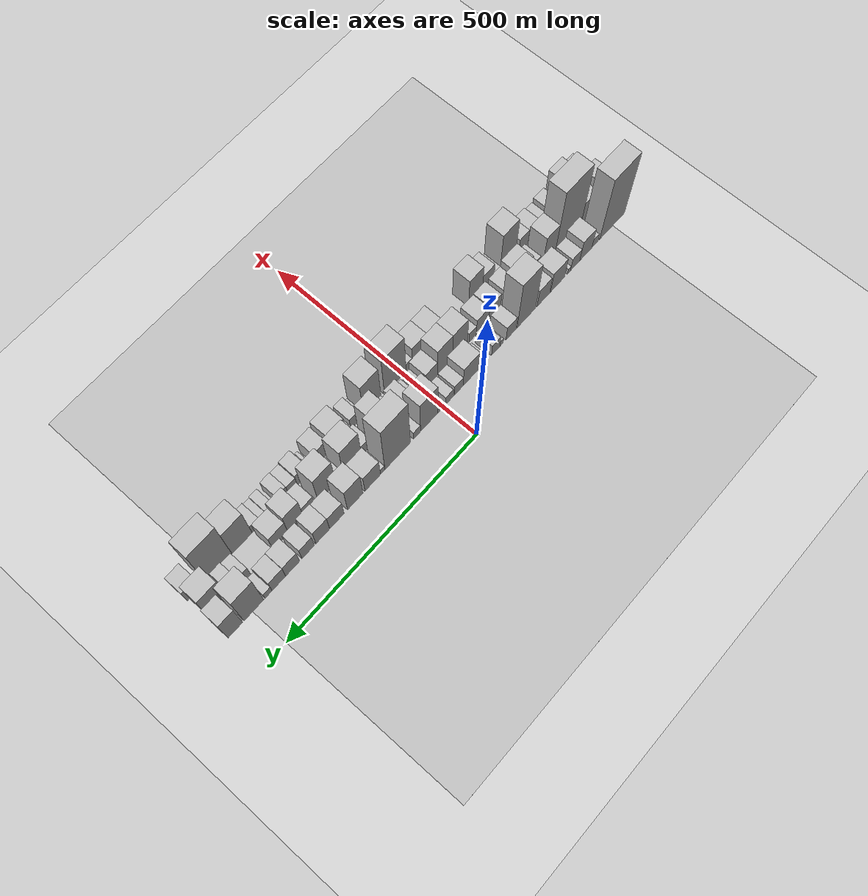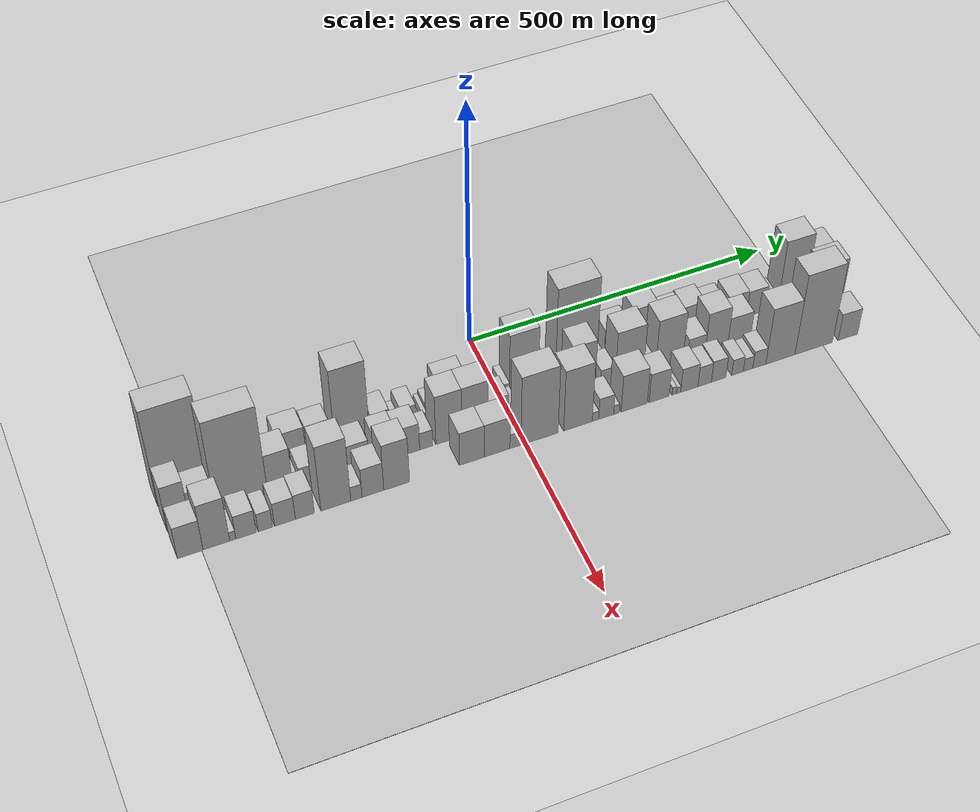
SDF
<?xml version="1.0" encoding="utf-8"?>

<sdf version="1.6">

   <world name="default">

      <gui fullscreen="0">

         <camera name="user_camera">

            <pose>-15 0 4.57585 0 0 0</pose>

            <view_controller>orbit</view_controller>

         </camera>

      </gui>

      <scene>

         <sky>

           <clouds>

             <speed>12</speed>

           </clouds>

         </sky>

         <ambient>0.4 0.4 0.4 1</ambient>

         <background>0.7 0.7 0.7 1</background>

         <shadows>1</shadows>

      </scene>

      <gravity>0 0 -9.8066</gravity>

      <magnetic_field>6e-06 2.3e-05 -4.2e-05</magnetic_field>

      <physics default="0" name="default_physics" type="ode">

         <ode>

            <solver>

               <type>quick</type>

               <iters>10</iters>

               <sor>1.0</sor>

               <use_dynamic_moi_rescaling>0</use_dynamic_moi_rescaling>

            </solver>

            <constraints>

               <cfm>0</cfm>

               <erp>0.2</erp>

               <contact_max_correcting_vel>100</contact_max_correcting_vel>

               <contact_surface_layer>0.001</contact_surface_layer>

            </constraints>

         </ode>

         <max_step_size>0.004</max_step_size>

         <real_time_factor>1</real_time_factor>

         <real_time_update_rate>250</real_time_update_rate>

      </physics>

      <light name="sun" type="directional">

         <cast_shadows>1</cast_shadows>

         <pose>0 0 10 0 0 0</pose>

         <diffuse>0.8 0.8 0.8 1</diffuse>

         <specular>0.2 0.2 0.2 1</specular>

         <attenuation>

            <range>1000</range>

            <constant>0.9</constant>

            <linear>0.01</linear>

            <quadratic>0.001</quadratic>

         </attenuation>

         <direction>-0.5 0.1 -0.9</direction>

      </light>

      <include>

         <name>ground_plane_1</name>

         <uri>model://HANNAS_ground_plane</uri>

         <pose>0 0 0  0 0 0</pose>

      </include>

      <include>

         <name>ground_plane_2</name>

         <uri>model://HANNAS_ground_plane</uri>

         <pose>100 0 0  0 0 0</pose>

      </include>

      <model name="building_1">

         <static>1</static>

         <pose frame="">100.0000 -496.9513 0 0.000000 0.000000 0.000000</pose>

         <link name="link">

            <pose frame="">0 0 109.50 0 0 0</pose>

            <collision name="collision">

               <geometry>

                  <box>

                     <size>40.0000 78.0974 219.0000</size>

                  </box>

               </geometry>

               <max_contacts>10</max_contacts>

               <surface>

                  <contact>

                     <ode/>

                  </contact>

                  <bounce/>

                  <friction>

                     <torsional>

                        <ode/>

                     </torsional>

                     <ode/>

                  </friction>

               </surface>

            </collision>

            <visual name="visual">

               <cast_shadows>0</cast_shadows>

               <geometry>

                  <box>

                     <size>40.0000 78.0974 219.0000</size>

                  </box>

               </geometry>

               <material>

                  <script>

                     <uri>model://HANNAS_wall/materials/scripts</uri>

                     <uri>model://HANNAS_wall/materials/textures</uri>

                     <name>vrc/HANNAS_wall</name>

                  </script>

               </material>

            </visual>

            <self_collide>0</self_collide>

            <enable_wind>0</enable_wind>

            <kinematic>0</kinematic>

         </link>

      </model>

      <model name="building_2">

         <static>1</static>

         <pose frame="">100.0000 -443.2013 0 0.000000 0.000000 0.000000</pose>

         <link name="link">

            <pose frame="">0 0 16.50 0 0 0</pose>

            <collision name="collision">

               <geometry>

                  <box>

                     <size>40.0000 17.4027 33.0000</size>

                  </box>

               </geometry>

               <max_contacts>10</max_contacts>

               <surface>

                  <contact>

                     <ode/>

                  </contact>

                  <bounce/>

                  <friction>

                     <torsional>

                        <ode/>

                     </torsional>

                     <ode/>

                  </friction>

               </surface>

            </collision>

            <visual name="visual">

               <cast_shadows>0</cast_shadows>

               <geometry>

                  <box>

                     <size>40.0000 17.4027 33.0000</size>

                  </box>

               </geometry>

               <material>

                  <script>

                     <uri>model://HANNAS_wall/materials/scripts</uri>

                     <uri>model://HANNAS_wall/materials/textures</uri>

                     <name>vrc/HANNAS_wall</name>

                  </script>

               </material>

            </visual>

            <self_collide>0</self_collide>

            <enable_wind>0</enable_wind>

            <kinematic>0</kinematic>

         </link>

      </model>

      <model name="building_3">

         <static>1</static>

         <pose frame="">100.0000 -415.7356 0 0.000000 0.000000 0.000000</pose>

         <link name="link">

            <pose frame="">0 0 37.50 0 0 0</pose>

            <collision name="collision">

               <geometry>

                  <box>

                     <size>40.0000 37.5286 75.0000</size>

                  </box>

               </geometry>

               <max_contacts>10</max_contacts>

               <surface>

                  <contact>

                     <ode/>

                  </contact>

                  <bounce/>

                  <friction>

                     <torsional>

                        <ode/>

                     </torsional>

                     <ode/>

                  </friction>

               </surface>

            </collision>

            <visual name="visual">

               <cast_shadows>0</cast_shadows>

               <geometry>

                  <box>

                     <size>40.0000 37.5286 75.0000</size>

                  </box>

               </geometry>

               <material>

                  <script>

                     <uri>model://HANNAS_wall/materials/scripts</uri>

                     <uri>model://HANNAS_wall/materials/textures</uri>

                     <name>vrc/HANNAS_wall</name>

                  </script>

               </material>

            </visual>

            <self_collide>0</self_collide>

            <enable_wind>0</enable_wind>

            <kinematic>0</kinematic>

         </link>

      </model>

      <model name="building_4">

         <static>1</static>

         <pose frame="">100.0000 -382.7974 0 0.000000 0.000000 0.000000</pose>

         <link name="link">

            <pose frame="">0 0 24.00 0 0 0</pose>

            <collision name="collision">

               <geometry>

                  <box>

                     <size>40.0000 28.3478 48.0000</size>

                  </box>

               </geometry>

               <max_contacts>10</max_contacts>

               <surface>

                  <contact>

                     <ode/>

                  </contact>

                  <bounce/>

                  <friction>

                     <torsional>

                        <ode/>

                     </torsional>

                     <ode/>

                  </friction>

               </surface>

            </collision>

            <visual name="visual">

               <cast_shadows>0</cast_shadows>

               <geometry>

                  <box>

                     <size>40.0000 28.3478 48.0000</size>

                  </box>

               </geometry>

               <material>

                  <script>

                     <uri>model://HANNAS_wall/materials/scripts</uri>

                     <uri>model://HANNAS_wall/materials/textures</uri>

                     <name>vrc/HANNAS_wall</name>

                  </script>

               </material>

            </visual>

            <self_collide>0</self_collide>

            <enable_wind>0</enable_wind>

            <kinematic>0</kinematic>

         </link>

      </model>

      <model name="building_5">

         <static>1</static>

         <pose frame="">100.0000 -364.3209 0 0.000000 0.000000 0.000000</pose>

         <link name="link">

            <pose frame="">0 0 10.50 0 0 0</pose>

            <collision name="collision">

               <geometry>

                  <box>

                     <size>40.0000 8.6052 21.0000</size>

                  </box>

               </geometry>

               <max_contacts>10</max_contacts>

               <surface>

                  <contact>

                     <ode/>

                  </contact>

                  <bounce/>

                  <friction>

                     <torsional>

                        <ode/>

                     </torsional>

                     <ode/>

                  </friction>

               </surface>

            </collision>

            <visual name="visual">

               <cast_shadows>0</cast_shadows>

               <geometry>

                  <box>

                     <size>40.0000 8.6052 21.0000</size>

                  </box>

               </geometry>

               <material>

                  <script>

                     <uri>model://HANNAS_wall/materials/scripts</uri>

                     <uri>model://HANNAS_wall/materials/textures</uri>

                     <name>vrc/HANNAS_wall</name>

                  </script>

               </material>

            </visual>

            <self_collide>0</self_collide>

            <enable_wind>0</enable_wind>

            <kinematic>0</kinematic>

         </link>

      </model>

      <model name="building_6">

         <static>1</static>

         <pose frame="">100.0000 -329.7746 0 0.000000 0.000000 0.000000</pose>

         <link name="link">

            <pose frame="">0 0 37.50 0 0 0</pose>

            <collision name="collision">

               <geometry>

                  <box>

                     <size>40.0000 42.4875 75.0000</size>

                  </box>

               </geometry>

               <max_contacts>10</max_contacts>

               <surface>

                  <contact>

                     <ode/>

                  </contact>

                  <bounce/>

                  <friction>

                     <torsional>

                        <ode/>

                     </torsional>

                     <ode/>

                  </friction>

               </surface>

            </collision>

            <visual name="visual">

               <cast_shadows>0</cast_shadows>

               <geometry>

                  <box>

                     <size>40.0000 42.4875 75.0000</size>

                  </box>

               </geometry>

               <material>

                  <script>

                     <uri>model://HANNAS_wall/materials/scripts</uri>

                     <uri>model://HANNAS_wall/materials/textures</uri>

                     <name>vrc/HANNAS_wall</name>

                  </script>

               </material>

            </visual>

            <self_collide>0</self_collide>

            <enable_wind>0</enable_wind>

            <kinematic>0</kinematic>

         </link>

      </model>

      <model name="building_7">

         <static>1</static>

         <pose frame="">100.0000 -287.1032 0 0.000000 0.000000 0.000000</pose>

         <link name="link">

            <pose frame="">0 0 33.00 0 0 0</pose>

            <collision name="collision">

               <geometry>

                  <box>

                     <size>40.0000 36.8551 66.0000</size>

                  </box>

               </geometry>

               <max_contacts>10</max_contacts>

               <surface>

                  <contact>

                     <ode/>

                  </contact>

                  <bounce/>

                  <friction>

                     <torsional>

                        <ode/>

                     </torsional>

                     <ode/>

                  </friction>

               </surface>

            </collision>

            <visual name="visual">

               <cast_shadows>0</cast_shadows>

               <geometry>

                  <box>

                     <size>40.0000 36.8551 66.0000</size>

                  </box>

               </geometry>

               <material>

                  <script>

                     <uri>model://HANNAS_wall/materials/scripts</uri>

                     <uri>model://HANNAS_wall/materials/textures</uri>

                     <name>vrc/HANNAS_wall</name>

                  </script>

               </material>

            </visual>

            <self_collide>0</self_collide>

            <enable_wind>0</enable_wind>

            <kinematic>0</kinematic>

         </link>

      </model>

      <model name="building_8">

         <static>1</static>

         <pose frame="">100.0000 -236.5073 0 0.000000 0.000000 0.000000</pose>

         <link name="link">

            <pose frame="">0 0 90.00 0 0 0</pose>

            <collision name="collision">

               <geometry>

                  <box>

                     <size>40.0000 54.3367 180.0000</size>

                  </box>

               </geometry>

               <max_contacts>10</max_contacts>

               <surface>

                  <contact>

                     <ode/>

                  </contact>

                  <bounce/>

                  <friction>

                     <torsional>

                        <ode/>

                     </torsional>

                     <ode/>

                  </friction>

               </surface>

            </collision>

            <visual name="visual">

               <cast_shadows>0</cast_shadows>

               <geometry>

                  <box>

                     <size>40.0000 54.3367 180.0000</size>

                  </box>

               </geometry>

               <material>

                  <script>

                     <uri>model://HANNAS_wall/materials/scripts</uri>

                     <uri>model://HANNAS_wall/materials/textures</uri>

                     <name>vrc/HANNAS_wall</name>

                  </script>

               </material>

            </visual>

            <self_collide>0</self_collide>

            <enable_wind>0</enable_wind>

            <kinematic>0</kinematic>

         </link>

      </model>

      <model name="building_9">

         <static>1</static>

         <pose frame="">100.0000 -191.7698 0 0.000000 0.000000 0.000000</pose>

         <link name="link">

            <pose frame="">0 0 27.00 0 0 0</pose>

            <collision name="collision">

               <geometry>

                  <box>

                     <size>40.0000 29.1382 54.0000</size>

                  </box>

               </geometry>

               <max_contacts>10</max_contacts>

               <surface>

                  <contact>

                     <ode/>

                  </contact>

                  <bounce/>

                  <friction>

                     <torsional>

                        <ode/>

                     </torsional>

                     <ode/>

                  </friction>

               </surface>

            </collision>

            <visual name="visual">

               <cast_shadows>0</cast_shadows>

               <geometry>

                  <box>

                     <size>40.0000 29.1382 54.0000</size>

                  </box>

               </geometry>

               <material>

                  <script>

                     <uri>model://HANNAS_wall/materials/scripts</uri>

                     <uri>model://HANNAS_wall/materials/textures</uri>

                     <name>vrc/HANNAS_wall</name>

                  </script>

               </material>

            </visual>

            <self_collide>0</self_collide>

            <enable_wind>0</enable_wind>

            <kinematic>0</kinematic>

         </link>

      </model>

      <model name="building_10">

         <static>1</static>

         <pose frame="">100.0000 -164.3954 0 0.000000 0.000000 0.000000</pose>

         <link name="link">

            <pose frame="">0 0 10.50 0 0 0</pose>

            <collision name="collision">

               <geometry>

                  <box>

                     <size>40.0000 9.6106 21.0000</size>

                  </box>

               </geometry>

               <max_contacts>10</max_contacts>

               <surface>

                  <contact>

                     <ode/>

                  </contact>

                  <bounce/>

                  <friction>

                     <torsional>

                        <ode/>

                     </torsional>

                     <ode/>

                  </friction>

               </surface>

            </collision>

            <visual name="visual">

               <cast_shadows>0</cast_shadows>

               <geometry>

                  <box>

                     <size>40.0000 9.6106 21.0000</size>

                  </box>

               </geometry>

               <material>

                  <script>

                     <uri>model://HANNAS_wall/materials/scripts</uri>

                     <uri>model://HANNAS_wall/materials/textures</uri>

                     <name>vrc/HANNAS_wall</name>

                  </script>

               </material>

            </visual>

            <self_collide>0</self_collide>

            <enable_wind>0</enable_wind>

            <kinematic>0</kinematic>

         </link>

      </model>

      <model name="building_11">

         <static>1</static>

         <pose frame="">100.0000 -147.4061 0 0.000000 0.000000 0.000000</pose>

         <link name="link">

            <pose frame="">0 0 22.50 0 0 0</pose>

            <collision name="collision">

               <geometry>

                  <box>

                     <size>40.0000 24.3681 45.0000</size>

                  </box>

               </geometry>

               <max_contacts>10</max_contacts>

               <surface>

                  <contact>

                     <ode/>

                  </contact>

                  <bounce/>

                  <friction>

                     <torsional>

                        <ode/>

                     </torsional>

                     <ode/>

                  </friction>

               </surface>

            </collision>

            <visual name="visual">

               <cast_shadows>0</cast_shadows>

               <geometry>

                  <box>

                     <size>40.0000 24.3681 45.0000</size>

                  </box>

               </geometry>

               <material>

                  <script>

                     <uri>model://HANNAS_wall/materials/scripts</uri>

                     <uri>model://HANNAS_wall/materials/textures</uri>

                     <name>vrc/HANNAS_wall</name>

                  </script>

               </material>

            </visual>

            <self_collide>0</self_collide>

            <enable_wind>0</enable_wind>

            <kinematic>0</kinematic>

         </link>

      </model>

      <model name="building_12">

         <static>1</static>

         <pose frame="">100.0000 -121.4864 0 0.000000 0.000000 0.000000</pose>

         <link name="link">

            <pose frame="">0 0 9.00 0 0 0</pose>

            <collision name="collision">

               <geometry>

                  <box>

                     <size>40.0000 7.4713 18.0000</size>

                  </box>

               </geometry>

               <max_contacts>10</max_contacts>

               <surface>

                  <contact>

                     <ode/>

                  </contact>

                  <bounce/>

                  <friction>

                     <torsional>

                        <ode/>

                     </torsional>

                     <ode/>

                  </friction>

               </surface>

            </collision>

            <visual name="visual">

               <cast_shadows>0</cast_shadows>

               <geometry>

                  <box>

                     <size>40.0000 7.4713 18.0000</size>

                  </box>

               </geometry>

               <material>

                  <script>

                     <uri>model://HANNAS_wall/materials/scripts</uri>

                     <uri>model://HANNAS_wall/materials/textures</uri>

                     <name>vrc/HANNAS_wall</name>

                  </script>

               </material>

            </visual>

            <self_collide>0</self_collide>

            <enable_wind>0</enable_wind>

            <kinematic>0</kinematic>

         </link>

      </model>

      <model name="building_13">

         <static>1</static>

         <pose frame="">100.0000 -111.4732 0 0.000000 0.000000 0.000000</pose>

         <link name="link">

            <pose frame="">0 0 13.50 0 0 0</pose>

            <collision name="collision">

               <geometry>

                  <box>

                     <size>40.0000 12.5551 27.0000</size>

                  </box>

               </geometry>

               <max_contacts>10</max_contacts>

               <surface>

                  <contact>

                     <ode/>

                  </contact>

                  <bounce/>

                  <friction>

                     <torsional>

                        <ode/>

                     </torsional>

                     <ode/>

                  </friction>

               </surface>

            </collision>

            <visual name="visual">

               <cast_shadows>0</cast_shadows>

               <geometry>

                  <box>

                     <size>40.0000 12.5551 27.0000</size>

                  </box>

               </geometry>

               <material>

                  <script>

                     <uri>model://HANNAS_wall/materials/scripts</uri>

                     <uri>model://HANNAS_wall/materials/textures</uri>

                     <name>vrc/HANNAS_wall</name>

                  </script>

               </material>

            </visual>

            <self_collide>0</self_collide>

            <enable_wind>0</enable_wind>

            <kinematic>0</kinematic>

         </link>

      </model>

      <model name="building_14">

         <static>1</static>

         <pose frame="">100.0000 -77.4347 0 0.000000 0.000000 0.000000</pose>

         <link name="link">

            <pose frame="">0 0 39.00 0 0 0</pose>

            <collision name="collision">

               <geometry>

                  <box>

                     <size>40.0000 45.5219 78.0000</size>

                  </box>

               </geometry>

               <max_contacts>10</max_contacts>

               <surface>

                  <contact>

                     <ode/>

                  </contact>

                  <bounce/>

                  <friction>

                     <torsional>

                        <ode/>

                     </torsional>

                     <ode/>

                  </friction>

               </surface>

            </collision>

            <visual name="visual">

               <cast_shadows>0</cast_shadows>

               <geometry>

                  <box>

                     <size>40.0000 45.5219 78.0000</size>

                  </box>

               </geometry>

               <material>

                  <script>

                     <uri>model://HANNAS_wall/materials/scripts</uri>

                     <uri>model://HANNAS_wall/materials/textures</uri>

                     <name>vrc/HANNAS_wall</name>

                  </script>

               </material>

            </visual>

            <self_collide>0</self_collide>

            <enable_wind>0</enable_wind>

            <kinematic>0</kinematic>

         </link>

      </model>

      <model name="building_15">

         <static>1</static>

         <pose frame="">100.0000 -42.3137 0 0.000000 0.000000 0.000000</pose>

         <link name="link">

            <pose frame="">0 0 21.00 0 0 0</pose>

            <collision name="collision">

               <geometry>

                  <box>

                     <size>40.0000 24.7201 42.0000</size>

                  </box>

               </geometry>

               <max_contacts>10</max_contacts>

               <surface>

                  <contact>

                     <ode/>

                  </contact>

                  <bounce/>

                  <friction>

                     <torsional>

                        <ode/>

                     </torsional>

                     <ode/>

                  </friction>

               </surface>

            </collision>

            <visual name="visual">

               <cast_shadows>0</cast_shadows>

               <geometry>

                  <box>

                     <size>40.0000 24.7201 42.0000</size>

                  </box>

               </geometry>

               <material>

                  <script>

                     <uri>model://HANNAS_wall/materials/scripts</uri>

                     <uri>model://HANNAS_wall/materials/textures</uri>

                     <name>vrc/HANNAS_wall</name>

                  </script>

               </material>

            </visual>

            <self_collide>0</self_collide>

            <enable_wind>0</enable_wind>

            <kinematic>0</kinematic>

         </link>

      </model>

      <model name="building_16">

         <static>1</static>

         <pose frame="">100.0000 -16.2429 0 0.000000 0.000000 0.000000</pose>

         <link name="link">

            <pose frame="">0 0 18.00 0 0 0</pose>

            <collision name="collision">

               <geometry>

                  <box>

                     <size>40.0000 21.4215 36.0000</size>

                  </box>

               </geometry>

               <max_contacts>10</max_contacts>

               <surface>

                  <contact>

                     <ode/>

                  </contact>

                  <bounce/>

                  <friction>

                     <torsional>

                        <ode/>

                     </torsional>

                     <ode/>

                  </friction>

               </surface>

            </collision>

            <visual name="visual">

               <cast_shadows>0</cast_shadows>

               <geometry>

                  <box>

                     <size>40.0000 21.4215 36.0000</size>

                  </box>

               </geometry>

               <material>

                  <script>

                     <uri>model://HANNAS_wall/materials/scripts</uri>

                     <uri>model://HANNAS_wall/materials/textures</uri>

                     <name>vrc/HANNAS_wall</name>

                  </script>

               </material>

            </visual>

            <self_collide>0</self_collide>

            <enable_wind>0</enable_wind>

            <kinematic>0</kinematic>

         </link>

      </model>

      <model name="building_17">

         <static>1</static>

         <pose frame="">100.0000 10.2576 0 0.000000 0.000000 0.000000</pose>

         <link name="link">

            <pose frame="">0 0 12.00 0 0 0</pose>

            <collision name="collision">

               <geometry>

                  <box>

                     <size>40.0000 11.5795 24.0000</size>

                  </box>

               </geometry>

               <max_contacts>10</max_contacts>

               <surface>

                  <contact>

                     <ode/>

                  </contact>

                  <bounce/>

                  <friction>

                     <torsional>

                        <ode/>

                     </torsional>

                     <ode/>

                  </friction>

               </surface>

            </collision>

            <visual name="visual">

               <cast_shadows>0</cast_shadows>

               <geometry>

                  <box>

                     <size>40.0000 11.5795 24.0000</size>

                  </box>

               </geometry>

               <material>

                  <script>

                     <uri>model://HANNAS_wall/materials/scripts</uri>

                     <uri>model://HANNAS_wall/materials/textures</uri>

                     <name>vrc/HANNAS_wall</name>

                  </script>

               </material>

            </visual>

            <self_collide>0</self_collide>

            <enable_wind>0</enable_wind>

            <kinematic>0</kinematic>

         </link>

      </model>

      <model name="building_18">

         <static>1</static>

         <pose frame="">100.0000 39.9462 0 0.000000 0.000000 0.000000</pose>

         <link name="link">

            <pose frame="">0 0 66.00 0 0 0</pose>

            <collision name="collision">

               <geometry>

                  <box>

                     <size>40.0000 47.7976 132.0000</size>

                  </box>

               </geometry>

               <max_contacts>10</max_contacts>

               <surface>

                  <contact>

                     <ode/>

                  </contact>

                  <bounce/>

                  <friction>

                     <torsional>

                        <ode/>

                     </torsional>

                     <ode/>

                  </friction>

               </surface>

            </collision>

            <visual name="visual">

               <cast_shadows>0</cast_shadows>

               <geometry>

                  <box>

                     <size>40.0000 47.7976 132.0000</size>

                  </box>

               </geometry>

               <material>

                  <script>

                     <uri>model://HANNAS_wall/materials/scripts</uri>

                     <uri>model://HANNAS_wall/materials/textures</uri>

                     <name>vrc/HANNAS_wall</name>

                  </script>

               </material>

            </visual>

            <self_collide>0</self_collide>

            <enable_wind>0</enable_wind>

            <kinematic>0</kinematic>

         </link>

      </model>

      <model name="building_19">

         <static>1</static>

         <pose frame="">100.0000 73.2808 0 0.000000 0.000000 0.000000</pose>

         <link name="link">

            <pose frame="">0 0 16.50 0 0 0</pose>

            <collision name="collision">

               <geometry>

                  <box>

                     <size>40.0000 18.8716 33.0000</size>

                  </box>

               </geometry>

               <max_contacts>10</max_contacts>

               <surface>

                  <contact>

                     <ode/>

                  </contact>

                  <bounce/>

                  <friction>

                     <torsional>

                        <ode/>

                     </torsional>

                     <ode/>

                  </friction>

               </surface>

            </collision>

            <visual name="visual">

               <cast_shadows>0</cast_shadows>

               <geometry>

                  <box>

                     <size>40.0000 18.8716 33.0000</size>

                  </box>

               </geometry>

               <material>

                  <script>

                     <uri>model://HANNAS_wall/materials/scripts</uri>

                     <uri>model://HANNAS_wall/materials/textures</uri>

                     <name>vrc/HANNAS_wall</name>

                  </script>

               </material>

            </visual>

            <self_collide>0</self_collide>

            <enable_wind>0</enable_wind>

            <kinematic>0</kinematic>

         </link>

      </model>

      <model name="building_20">

         <static>1</static>

         <pose frame="">100.0000 126.0601 0 0.000000 0.000000 0.000000</pose>

         <link name="link">

            <pose frame="">0 0 100.50 0 0 0</pose>

            <collision name="collision">

               <geometry>

                  <box>

                     <size>40.0000 68.6869 201.0000</size>

                  </box>

               </geometry>

               <max_contacts>10</max_contacts>

               <surface>

                  <contact>

                     <ode/>

                  </contact>

                  <bounce/>

                  <friction>

                     <torsional>

                        <ode/>

                     </torsional>

                     <ode/>

                  </friction>

               </surface>

            </collision>

            <visual name="visual">

               <cast_shadows>0</cast_shadows>

               <geometry>

                  <box>

                     <size>40.0000 68.6869 201.0000</size>

                  </box>

               </geometry>

               <material>

                  <script>

                     <uri>model://HANNAS_wall/materials/scripts</uri>

                     <uri>model://HANNAS_wall/materials/textures</uri>

                     <name>vrc/HANNAS_wall</name>

                  </script>

               </material>

            </visual>

            <self_collide>0</self_collide>

            <enable_wind>0</enable_wind>

            <kinematic>0</kinematic>

         </link>

      </model>

      <model name="building_21">

         <static>1</static>

         <pose frame="">100.0000 166.3277 0 0.000000 0.000000 0.000000</pose>

         <link name="link">

            <pose frame="">0 0 12.00 0 0 0</pose>

            <collision name="collision">

               <geometry>

                  <box>

                     <size>40.0000 11.8484 24.0000</size>

                  </box>

               </geometry>

               <max_contacts>10</max_contacts>

               <surface>

                  <contact>

                     <ode/>

                  </contact>

                  <bounce/>

                  <friction>

                     <torsional>

                        <ode/>

                     </torsional>

                     <ode/>

                  </friction>

               </surface>

            </collision>

            <visual name="visual">

               <cast_shadows>0</cast_shadows>

               <geometry>

                  <box>

                     <size>40.0000 11.8484 24.0000</size>

                  </box>

               </geometry>

               <material>

                  <script>

                     <uri>model://HANNAS_wall/materials/scripts</uri>

                     <uri>model://HANNAS_wall/materials/textures</uri>

                     <name>vrc/HANNAS_wall</name>

                  </script>

               </material>

            </visual>

            <self_collide>0</self_collide>

            <enable_wind>0</enable_wind>

            <kinematic>0</kinematic>

         </link>

      </model>

      <model name="building_22">

         <static>1</static>

         <pose frame="">100.0000 192.9330 0 0.000000 0.000000 0.000000</pose>

         <link name="link">

            <pose frame="">0 0 37.50 0 0 0</pose>

            <collision name="collision">

               <geometry>

                  <box>

                     <size>40.0000 41.3621 75.0000</size>

                  </box>

               </geometry>

               <max_contacts>10</max_contacts>

               <surface>

                  <contact>

                     <ode/>

                  </contact>

                  <bounce/>

                  <friction>

                     <torsional>

                        <ode/>

                     </torsional>

                     <ode/>

                  </friction>

               </surface>

            </collision>

            <visual name="visual">

               <cast_shadows>0</cast_shadows>

               <geometry>

                  <box>

                     <size>40.0000 41.3621 75.0000</size>

                  </box>

               </geometry>

               <material>

                  <script>

                     <uri>model://HANNAS_wall/materials/scripts</uri>

                     <uri>model://HANNAS_wall/materials/textures</uri>

                     <name>vrc/HANNAS_wall</name>

                  </script>

               </material>

            </visual>

            <self_collide>0</self_collide>

            <enable_wind>0</enable_wind>

            <kinematic>0</kinematic>

         </link>

      </model>

      <model name="building_23">

         <static>1</static>

         <pose frame="">100.0000 238.8973 0 0.000000 0.000000 0.000000</pose>

         <link name="link">

            <pose frame="">0 0 51.00 0 0 0</pose>

            <collision name="collision">

               <geometry>

                  <box>

                     <size>40.0000 40.5665 102.0000</size>

                  </box>

               </geometry>

               <max_contacts>10</max_contacts>

               <surface>

                  <contact>

                     <ode/>

                  </contact>

                  <bounce/>

                  <friction>

                     <torsional>

                        <ode/>

                     </torsional>

                     <ode/>

                  </friction>

               </surface>

            </collision>

            <visual name="visual">

               <cast_shadows>0</cast_shadows>

               <geometry>

                  <box>

                     <size>40.0000 40.5665 102.0000</size>

                  </box>

               </geometry>

               <material>

                  <script>

                     <uri>model://HANNAS_wall/materials/scripts</uri>

                     <uri>model://HANNAS_wall/materials/textures</uri>

                     <name>vrc/HANNAS_wall</name>

                  </script>

               </material>

            </visual>

            <self_collide>0</self_collide>

            <enable_wind>0</enable_wind>

            <kinematic>0</kinematic>

         </link>

      </model>

      <model name="building_24">

         <static>1</static>

         <pose frame="">100.0000 286.8793 0 0.000000 0.000000 0.000000</pose>

         <link name="link">

            <pose frame="">0 0 33.00 0 0 0</pose>

            <collision name="collision">

               <geometry>

                  <box>

                     <size>40.0000 37.3974 66.0000</size>

                  </box>

               </geometry>

               <max_contacts>10</max_contacts>

               <surface>

                  <contact>

                     <ode/>

                  </contact>

                  <bounce/>

                  <friction>

                     <torsional>

                        <ode/>

                     </torsional>

                     <ode/>

                  </friction>

               </surface>

            </collision>

            <visual name="visual">

               <cast_shadows>0</cast_shadows>

               <geometry>

                  <box>

                     <size>40.0000 37.3974 66.0000</size>

                  </box>

               </geometry>

               <material>

                  <script>

                     <uri>model://HANNAS_wall/materials/scripts</uri>

                     <uri>model://HANNAS_wall/materials/textures</uri>

                     <name>vrc/HANNAS_wall</name>

                  </script>

               </material>

            </visual>

            <self_collide>0</self_collide>

            <enable_wind>0</enable_wind>

            <kinematic>0</kinematic>

         </link>

      </model>

      <model name="building_25">

         <static>1</static>

         <pose frame="">100.0000 323.3597 0 0.000000 0.000000 0.000000</pose>

         <link name="link">

            <pose frame="">0 0 34.50 0 0 0</pose>

            <collision name="collision">

               <geometry>

                  <box>

                     <size>40.0000 35.5632 69.0000</size>

                  </box>

               </geometry>

               <max_contacts>10</max_contacts>

               <surface>

                  <contact>

                     <ode/>

                  </contact>

                  <bounce/>

                  <friction>

                     <torsional>

                        <ode/>

                     </torsional>

                     <ode/>

                  </friction>

               </surface>

            </collision>

            <visual name="visual">

               <cast_shadows>0</cast_shadows>

               <geometry>

                  <box>

                     <size>40.0000 35.5632 69.0000</size>

                  </box>

               </geometry>

               <material>

                  <script>

                     <uri>model://HANNAS_wall/materials/scripts</uri>

                     <uri>model://HANNAS_wall/materials/textures</uri>

                     <name>vrc/HANNAS_wall</name>

                  </script>

               </material>

            </visual>

            <self_collide>0</self_collide>

            <enable_wind>0</enable_wind>

            <kinematic>0</kinematic>

         </link>

      </model>

      <model name="building_26">

         <static>1</static>

         <pose frame="">100.0000 360.8102 0 0.000000 0.000000 0.000000</pose>

         <link name="link">

            <pose frame="">0 0 28.50 0 0 0</pose>

            <collision name="collision">

               <geometry>

                  <box>

                     <size>40.0000 31.3379 57.0000</size>

                  </box>

               </geometry>

               <max_contacts>10</max_contacts>

               <surface>

                  <contact>

                     <ode/>

                  </contact>

                  <bounce/>

                  <friction>

                     <torsional>

                        <ode/>

                     </torsional>

                     <ode/>

                  </friction>

               </surface>

            </collision>

            <visual name="visual">

               <cast_shadows>0</cast_shadows>

               <geometry>

                  <box>

                     <size>40.0000 31.3379 57.0000</size>

                  </box>

               </geometry>

               <material>

                  <script>

                     <uri>model://HANNAS_wall/materials/scripts</uri>

                     <uri>model://HANNAS_wall/materials/textures</uri>

                     <name>vrc/HANNAS_wall</name>

                  </script>

               </material>

            </visual>

            <self_collide>0</self_collide>

            <enable_wind>0</enable_wind>

            <kinematic>0</kinematic>

         </link>

      </model>

      <model name="building_27">

         <static>1</static>

         <pose frame="">100.0000 400.1035 0 0.000000 0.000000 0.000000</pose>

         <link name="link">

            <pose frame="">0 0 30.00 0 0 0</pose>

            <collision name="collision">

               <geometry>

                  <box>

                     <size>40.0000 35.2487 60.0000</size>

                  </box>

               </geometry>

               <max_contacts>10</max_contacts>

               <surface>

                  <contact>

                     <ode/>

                  </contact>

                  <bounce/>

                  <friction>

                     <torsional>

                        <ode/>

                     </torsional>

                     <ode/>

                  </friction>

               </surface>

            </collision>

            <visual name="visual">

               <cast_shadows>0</cast_shadows>

               <geometry>

                  <box>

                     <size>40.0000 35.2487 60.0000</size>

                  </box>

               </geometry>

               <material>

                  <script>

                     <uri>model://HANNAS_wall/materials/scripts</uri>

                     <uri>model://HANNAS_wall/materials/textures</uri>

                     <name>vrc/HANNAS_wall</name>

                  </script>

               </material>

            </visual>

            <self_collide>0</self_collide>

            <enable_wind>0</enable_wind>

            <kinematic>0</kinematic>

         </link>

      </model>

      <model name="building_28">

         <static>1</static>

         <pose frame="">100.0000 434.7161 0 0.000000 0.000000 0.000000</pose>

         <link name="link">

            <pose frame="">0 0 28.50 0 0 0</pose>

            <collision name="collision">

               <geometry>

                  <box>

                     <size>40.0000 33.9765 57.0000</size>

                  </box>

               </geometry>

               <max_contacts>10</max_contacts>

               <surface>

                  <contact>

                     <ode/>

                  </contact>

                  <bounce/>

                  <friction>

                     <torsional>

                        <ode/>

                     </torsional>

                     <ode/>

                  </friction>

               </surface>

            </collision>

            <visual name="visual">

               <cast_shadows>0</cast_shadows>

               <geometry>

                  <box>

                     <size>40.0000 33.9765 57.0000</size>

                  </box>

               </geometry>

               <material>

                  <script>

                     <uri>model://HANNAS_wall/materials/scripts</uri>

                     <uri>model://HANNAS_wall/materials/textures</uri>

                     <name>vrc/HANNAS_wall</name>

                  </script>

               </material>

            </visual>

            <self_collide>0</self_collide>

            <enable_wind>0</enable_wind>

            <kinematic>0</kinematic>

         </link>

      </model>

      <model name="building_29">

         <static>1</static>

         <pose frame="">100.0000 460.5579 0 0.000000 0.000000 0.000000</pose>

         <link name="link">

            <pose frame="">0 0 15.00 0 0 0</pose>

            <collision name="collision">

               <geometry>

                  <box>

                     <size>40.0000 17.7070 30.0000</size>

                  </box>

               </geometry>

               <max_contacts>10</max_contacts>

               <surface>

                  <contact>

                     <ode/>

                  </contact>

                  <bounce/>

                  <friction>

                     <torsional>

                        <ode/>

                     </torsional>

                     <ode/>

                  </friction>

               </surface>

            </collision>

            <visual name="visual">

               <cast_shadows>0</cast_shadows>

               <geometry>

                  <box>

                     <size>40.0000 17.7070 30.0000</size>

                  </box>

               </geometry>

               <material>

                  <script>

                     <uri>model://HANNAS_wall/materials/scripts</uri>

                     <uri>model://HANNAS_wall/materials/textures</uri>

                     <name>vrc/HANNAS_wall</name>

                  </script>

               </material>

            </visual>

            <self_collide>0</self_collide>

            <enable_wind>0</enable_wind>

            <kinematic>0</kinematic>

         </link>

      </model>

      <model name="building_30">

         <static>1</static>

         <pose frame="">100.0000 496.8309 0 0.000000 0.000000 0.000000</pose>

         <link name="link">

            <pose frame="">0 0 73.50 0 0 0</pose>

            <collision name="collision">

               <geometry>

                  <box>

                     <size>40.0000 48.8391 147.0000</size>

                  </box>

               </geometry>

               <max_contacts>10</max_contacts>

               <surface>

                  <contact>

                     <ode/>

                  </contact>

                  <bounce/>

                  <friction>

                     <torsional>

                        <ode/>

                     </torsional>

                     <ode/>

                  </friction>

               </surface>

            </collision>

            <visual name="visual">

               <cast_shadows>0</cast_shadows>

               <geometry>

                  <box>

                     <size>40.0000 48.8391 147.0000</size>

                  </box>

               </geometry>

               <material>

                  <script>

                     <uri>model://HANNAS_wall/materials/scripts</uri>

                     <uri>model://HANNAS_wall/materials/textures</uri>

                     <name>vrc/HANNAS_wall</name>

                  </script>

               </material>

            </visual>

            <self_collide>0</self_collide>

            <enable_wind>0</enable_wind>

            <kinematic>0</kinematic>

         </link>

      </model>

      <model name="building_31">

         <static>1</static>

         <pose frame="">100.0000 542.0296 0 0.000000 0.000000 0.000000</pose>

         <link name="link">

            <pose frame="">0 0 54.00 0 0 0</pose>

            <collision name="collision">

               <geometry>

                  <box>

                     <size>40.0000 35.5582 108.0000</size>

                  </box>

               </geometry>

               <max_contacts>10</max_contacts>

               <surface>

                  <contact>

                     <ode/>

                  </contact>

                  <bounce/>

                  <friction>

                     <torsional>

                        <ode/>

                     </torsional>

                     <ode/>

                  </friction>

               </surface>

            </collision>

            <visual name="visual">

               <cast_shadows>0</cast_shadows>

               <geometry>

                  <box>

                     <size>40.0000 35.5582 108.0000</size>

                  </box>

               </geometry>

               <material>

                  <script>

                     <uri>model://HANNAS_wall/materials/scripts</uri>

                     <uri>model://HANNAS_wall/materials/textures</uri>

                     <name>vrc/HANNAS_wall</name>

                  </script>

               </material>

            </visual>

            <self_collide>0</self_collide>

            <enable_wind>0</enable_wind>

            <kinematic>0</kinematic>

         </link>

      </model>

      <model name="building_32">

         <static>1</static>

         <pose frame="">149.0000 -518.9224 0 0.000000 0.000000 0.000000</pose>

         <link name="link">

            <pose frame="">0 0 52.50 0 0 0</pose>

            <collision name="collision">

               <geometry>

                  <box>

                     <size>40.0000 34.1551 105.0000</size>

                  </box>

               </geometry>

               <max_contacts>10</max_contacts>

               <surface>

                  <contact>

                     <ode/>

                  </contact>

                  <bounce/>

                  <friction>

                     <torsional>

                        <ode/>

                     </torsional>

                     <ode/>

                  </friction>

               </surface>

            </collision>

            <visual name="visual">

               <cast_shadows>0</cast_shadows>

               <geometry>

                  <box>

                     <size>40.0000 34.1551 105.0000</size>

                  </box>

               </geometry>

               <material>

                  <script>

                     <uri>model://HANNAS_wall/materials/scripts</uri>

                     <uri>model://HANNAS_wall/materials/textures</uri>

                     <name>vrc/HANNAS_wall</name>

                  </script>

               </material>

            </visual>

            <self_collide>0</self_collide>

            <enable_wind>0</enable_wind>

            <kinematic>0</kinematic>

         </link>

      </model>

      <model name="building_33">

         <static>1</static>

         <pose frame="">149.0000 -482.2454 0 0.000000 0.000000 0.000000</pose>

         <link name="link">

            <pose frame="">0 0 37.50 0 0 0</pose>

            <collision name="collision">

               <geometry>

                  <box>

                     <size>40.0000 39.1991 75.0000</size>

                  </box>

               </geometry>

               <max_contacts>10</max_contacts>

               <surface>

                  <contact>

                     <ode/>

                  </contact>

                  <bounce/>

                  <friction>

                     <torsional>

                        <ode/>

                     </torsional>

                     <ode/>

                  </friction>

               </surface>

            </collision>

            <visual name="visual">

               <cast_shadows>0</cast_shadows>

               <geometry>

                  <box>

                     <size>40.0000 39.1991 75.0000</size>

                  </box>

               </geometry>

               <material>

                  <script>

                     <uri>model://HANNAS_wall/materials/scripts</uri>

                     <uri>model://HANNAS_wall/materials/textures</uri>

                     <name>vrc/HANNAS_wall</name>

                  </script>

               </material>

            </visual>

            <self_collide>0</self_collide>

            <enable_wind>0</enable_wind>

            <kinematic>0</kinematic>

         </link>

      </model>

      <model name="building_34">

         <static>1</static>

         <pose frame="">149.0000 -423.0927 0 0.000000 0.000000 0.000000</pose>

         <link name="link">

            <pose frame="">0 0 108.00 0 0 0</pose>

            <collision name="collision">

               <geometry>

                  <box>

                     <size>40.0000 79.1063 216.0000</size>

                  </box>

               </geometry>

               <max_contacts>10</max_contacts>

               <surface>

                  <contact>

                     <ode/>

                  </contact>

                  <bounce/>

                  <friction>

                     <torsional>

                        <ode/>

                     </torsional>

                     <ode/>

                  </friction>

               </surface>

            </collision>

            <visual name="visual">

               <cast_shadows>0</cast_shadows>

               <geometry>

                  <box>

                     <size>40.0000 79.1063 216.0000</size>

                  </box>

               </geometry>

               <material>

                  <script>

                     <uri>model://HANNAS_wall/materials/scripts</uri>

                     <uri>model://HANNAS_wall/materials/textures</uri>

                     <name>vrc/HANNAS_wall</name>

                  </script>

               </material>

            </visual>

            <self_collide>0</self_collide>

            <enable_wind>0</enable_wind>

            <kinematic>0</kinematic>

         </link>

      </model>

      <model name="building_35">

         <static>1</static>

         <pose frame="">149.0000 -364.4525 0 0.000000 0.000000 0.000000</pose>

         <link name="link">

            <pose frame="">0 0 51.00 0 0 0</pose>

            <collision name="collision">

               <geometry>

                  <box>

                     <size>40.0000 38.1742 102.0000</size>

                  </box>

               </geometry>

               <max_contacts>10</max_contacts>

               <surface>

                  <contact>

                     <ode/>

                  </contact>

                  <bounce/>

                  <friction>

                     <torsional>

                        <ode/>

                     </torsional>

                     <ode/>

                  </friction>

               </surface>

            </collision>

            <visual name="visual">

               <cast_shadows>0</cast_shadows>

               <geometry>

                  <box>

                     <size>40.0000 38.1742 102.0000</size>

                  </box>

               </geometry>

               <material>

                  <script>

                     <uri>model://HANNAS_wall/materials/scripts</uri>

                     <uri>model://HANNAS_wall/materials/textures</uri>

                     <name>vrc/HANNAS_wall</name>

                  </script>

               </material>

            </visual>

            <self_collide>0</self_collide>

            <enable_wind>0</enable_wind>

            <kinematic>0</kinematic>

         </link>

      </model>

      <model name="building_36">

         <static>1</static>

         <pose frame="">149.0000 -340.2074 0 0.000000 0.000000 0.000000</pose>

         <link name="link">

            <pose frame="">0 0 12.00 0 0 0</pose>

            <collision name="collision">

               <geometry>

                  <box>

                     <size>40.0000 10.3160 24.0000</size>

                  </box>

               </geometry>

               <max_contacts>10</max_contacts>

               <surface>

                  <contact>

                     <ode/>

                  </contact>

                  <bounce/>

                  <friction>

                     <torsional>

                        <ode/>

                     </torsional>

                     <ode/>

                  </friction>

               </surface>

            </collision>

            <visual name="visual">

               <cast_shadows>0</cast_shadows>

               <geometry>

                  <box>

                     <size>40.0000 10.3160 24.0000</size>

                  </box>

               </geometry>

               <material>

                  <script>

                     <uri>model://HANNAS_wall/materials/scripts</uri>

                     <uri>model://HANNAS_wall/materials/textures</uri>

                     <name>vrc/HANNAS_wall</name>

                  </script>

               </material>

            </visual>

            <self_collide>0</self_collide>

            <enable_wind>0</enable_wind>

            <kinematic>0</kinematic>

         </link>

      </model>

      <model name="building_37">

         <static>1</static>

         <pose frame="">149.0000 -321.8063 0 0.000000 0.000000 0.000000</pose>

         <link name="link">

            <pose frame="">0 0 24.00 0 0 0</pose>

            <collision name="collision">

               <geometry>

                  <box>

                     <size>40.0000 26.4862 48.0000</size>

                  </box>

               </geometry>

               <max_contacts>10</max_contacts>

               <surface>

                  <contact>

                     <ode/>

                  </contact>

                  <bounce/>

                  <friction>

                     <torsional>

                        <ode/>

                     </torsional>

                     <ode/>

                  </friction>

               </surface>

            </collision>

            <visual name="visual">

               <cast_shadows>0</cast_shadows>

               <geometry>

                  <box>

                     <size>40.0000 26.4862 48.0000</size>

                  </box>

               </geometry>

               <material>

                  <script>

                     <uri>model://HANNAS_wall/materials/scripts</uri>

                     <uri>model://HANNAS_wall/materials/textures</uri>

                     <name>vrc/HANNAS_wall</name>

                  </script>

               </material>

            </visual>

            <self_collide>0</self_collide>

            <enable_wind>0</enable_wind>

            <kinematic>0</kinematic>

         </link>

      </model>

      <model name="building_38">

         <static>1</static>

         <pose frame="">149.0000 -285.0739 0 0.000000 0.000000 0.000000</pose>

         <link name="link">

            <pose frame="">0 0 43.50 0 0 0</pose>

            <collision name="collision">

               <geometry>

                  <box>

                     <size>40.0000 46.9787 87.0000</size>

                  </box>

               </geometry>

               <max_contacts>10</max_contacts>

               <surface>

                  <contact>

                     <ode/>

                  </contact>

                  <bounce/>

                  <friction>

                     <torsional>

                        <ode/>

                     </torsional>

                     <ode/>

                  </friction>

               </surface>

            </collision>

            <visual name="visual">

               <cast_shadows>0</cast_shadows>

               <geometry>

                  <box>

                     <size>40.0000 46.9787 87.0000</size>

                  </box>

               </geometry>

               <material>

                  <script>

                     <uri>model://HANNAS_wall/materials/scripts</uri>

                     <uri>model://HANNAS_wall/materials/textures</uri>

                     <name>vrc/HANNAS_wall</name>

                  </script>

               </material>

            </visual>

            <self_collide>0</self_collide>

            <enable_wind>0</enable_wind>

            <kinematic>0</kinematic>

         </link>

      </model>

      <model name="building_39">

         <static>1</static>

         <pose frame="">149.0000 -244.6582 0 0.000000 0.000000 0.000000</pose>

         <link name="link">

            <pose frame="">0 0 31.50 0 0 0</pose>

            <collision name="collision">

               <geometry>

                  <box>

                     <size>40.0000 33.8528 63.0000</size>

                  </box>

               </geometry>

               <max_contacts>10</max_contacts>

               <surface>

                  <contact>

                     <ode/>

                  </contact>

                  <bounce/>

                  <friction>

                     <torsional>

                        <ode/>

                     </torsional>

                     <ode/>

                  </friction>

               </surface>

            </collision>

            <visual name="visual">

               <cast_shadows>0</cast_shadows>

               <geometry>

                  <box>

                     <size>40.0000 33.8528 63.0000</size>

                  </box>

               </geometry>

               <material>

                  <script>

                     <uri>model://HANNAS_wall/materials/scripts</uri>

                     <uri>model://HANNAS_wall/materials/textures</uri>

                     <name>vrc/HANNAS_wall</name>

                  </script>

               </material>

            </visual>

            <self_collide>0</self_collide>

            <enable_wind>0</enable_wind>

            <kinematic>0</kinematic>

         </link>

      </model>

      <model name="building_40">

         <static>1</static>

         <pose frame="">149.0000 -201.6952 0 0.000000 0.000000 0.000000</pose>

         <link name="link">

            <pose frame="">0 0 33.00 0 0 0</pose>

            <collision name="collision">

               <geometry>

                  <box>

                     <size>40.0000 34.0731 66.0000</size>

                  </box>

               </geometry>

               <max_contacts>10</max_contacts>

               <surface>

                  <contact>

                     <ode/>

                  </contact>

                  <bounce/>

                  <friction>

                     <torsional>

                        <ode/>

                     </torsional>

                     <ode/>

                  </friction>

               </surface>

            </collision>

            <visual name="visual">

               <cast_shadows>0</cast_shadows>

               <geometry>

                  <box>

                     <size>40.0000 34.0731 66.0000</size>

                  </box>

               </geometry>

               <material>

                  <script>

                     <uri>model://HANNAS_wall/materials/scripts</uri>

                     <uri>model://HANNAS_wall/materials/textures</uri>

                     <name>vrc/HANNAS_wall</name>

                  </script>

               </material>

            </visual>

            <self_collide>0</self_collide>

            <enable_wind>0</enable_wind>

            <kinematic>0</kinematic>

         </link>

      </model>

      <model name="building_41">

         <static>1</static>

         <pose frame="">149.0000 -166.7719 0 0.000000 0.000000 0.000000</pose>

         <link name="link">

            <pose frame="">0 0 31.50 0 0 0</pose>

            <collision name="collision">

               <geometry>

                  <box>

                     <size>40.0000 35.7736 63.0000</size>

                  </box>

               </geometry>

               <max_contacts>10</max_contacts>

               <surface>

                  <contact>

                     <ode/>

                  </contact>

                  <bounce/>

                  <friction>

                     <torsional>

                        <ode/>

                     </torsional>

                     <ode/>

                  </friction>

               </surface>

            </collision>

            <visual name="visual">

               <cast_shadows>0</cast_shadows>

               <geometry>

                  <box>

                     <size>40.0000 35.7736 63.0000</size>

                  </box>

               </geometry>

               <material>

                  <script>

                     <uri>model://HANNAS_wall/materials/scripts</uri>

                     <uri>model://HANNAS_wall/materials/textures</uri>

                     <name>vrc/HANNAS_wall</name>

                  </script>

               </material>

            </visual>

            <self_collide>0</self_collide>

            <enable_wind>0</enable_wind>

            <kinematic>0</kinematic>

         </link>

      </model>

      <model name="building_42">

         <static>1</static>

         <pose frame="">149.0000 -138.5100 0 0.000000 0.000000 0.000000</pose>

         <link name="link">

            <pose frame="">0 0 19.50 0 0 0</pose>

            <collision name="collision">

               <geometry>

                  <box>

                     <size>40.0000 20.7500 39.0000</size>

                  </box>

               </geometry>

               <max_contacts>10</max_contacts>

               <surface>

                  <contact>

                     <ode/>

                  </contact>

                  <bounce/>

                  <friction>

                     <torsional>

                        <ode/>

                     </torsional>

                     <ode/>

                  </friction>

               </surface>

            </collision>

            <visual name="visual">

               <cast_shadows>0</cast_shadows>

               <geometry>

                  <box>

                     <size>40.0000 20.7500 39.0000</size>

                  </box>

               </geometry>

               <material>

                  <script>

                     <uri>model://HANNAS_wall/materials/scripts</uri>

                     <uri>model://HANNAS_wall/materials/textures</uri>

                     <name>vrc/HANNAS_wall</name>

                  </script>

               </material>

            </visual>

            <self_collide>0</self_collide>

            <enable_wind>0</enable_wind>

            <kinematic>0</kinematic>

         </link>

      </model>

      <model name="building_43">

         <static>1</static>

         <pose frame="">149.0000 -102.0988 0 0.000000 0.000000 0.000000</pose>

         <link name="link">

            <pose frame="">0 0 55.50 0 0 0</pose>

            <collision name="collision">

               <geometry>

                  <box>

                     <size>40.0000 42.0724 111.0000</size>

                  </box>

               </geometry>

               <max_contacts>10</max_contacts>

               <surface>

                  <contact>

                     <ode/>

                  </contact>

                  <bounce/>

                  <friction>

                     <torsional>

                        <ode/>

                     </torsional>

                     <ode/>

                  </friction>

               </surface>

            </collision>

            <visual name="visual">

               <cast_shadows>0</cast_shadows>

               <geometry>

                  <box>

                     <size>40.0000 42.0724 111.0000</size>

                  </box>

               </geometry>

               <material>

                  <script>

                     <uri>model://HANNAS_wall/materials/scripts</uri>

                     <uri>model://HANNAS_wall/materials/textures</uri>

                     <name>vrc/HANNAS_wall</name>

                  </script>

               </material>

            </visual>

            <self_collide>0</self_collide>

            <enable_wind>0</enable_wind>

            <kinematic>0</kinematic>

         </link>

      </model>

      <model name="building_44">

         <static>1</static>

         <pose frame="">149.0000 -60.1409 0 0.000000 0.000000 0.000000</pose>

         <link name="link">

            <pose frame="">0 0 55.50 0 0 0</pose>

            <collision name="collision">

               <geometry>

                  <box>

                     <size>40.0000 41.8435 111.0000</size>

                  </box>

               </geometry>

               <max_contacts>10</max_contacts>

               <surface>

                  <contact>

                     <ode/>

                  </contact>

                  <bounce/>

                  <friction>

                     <torsional>

                        <ode/>

                     </torsional>

                     <ode/>

                  </friction>

               </surface>

            </collision>

            <visual name="visual">

               <cast_shadows>0</cast_shadows>

               <geometry>

                  <box>

                     <size>40.0000 41.8435 111.0000</size>

                  </box>

               </geometry>

               <material>

                  <script>

                     <uri>model://HANNAS_wall/materials/scripts</uri>

                     <uri>model://HANNAS_wall/materials/textures</uri>

                     <name>vrc/HANNAS_wall</name>

                  </script>

               </material>

            </visual>

            <self_collide>0</self_collide>

            <enable_wind>0</enable_wind>

            <kinematic>0</kinematic>

         </link>

      </model>

      <model name="building_45">

         <static>1</static>

         <pose frame="">149.0000 -22.5852 0 0.000000 0.000000 0.000000</pose>

         <link name="link">

            <pose frame="">0 0 31.50 0 0 0</pose>

            <collision name="collision">

               <geometry>

                  <box>

                     <size>40.0000 33.2679 63.0000</size>

                  </box>

               </geometry>

               <max_contacts>10</max_contacts>

               <surface>

                  <contact>

                     <ode/>

                  </contact>

                  <bounce/>

                  <friction>

                     <torsional>

                        <ode/>

                     </torsional>

                     <ode/>

                  </friction>

               </surface>

            </collision>

            <visual name="visual">

               <cast_shadows>0</cast_shadows>

               <geometry>

                  <box>

                     <size>40.0000 33.2679 63.0000</size>

                  </box>

               </geometry>

               <material>

                  <script>

                     <uri>model://HANNAS_wall/materials/scripts</uri>

                     <uri>model://HANNAS_wall/materials/textures</uri>

                     <name>vrc/HANNAS_wall</name>

                  </script>

               </material>

            </visual>

            <self_collide>0</self_collide>

            <enable_wind>0</enable_wind>

            <kinematic>0</kinematic>

         </link>

      </model>

      <model name="building_46">

         <static>1</static>

         <pose frame="">149.0000 2.7122 0 0.000000 0.000000 0.000000</pose>

         <link name="link">

            <pose frame="">0 0 15.00 0 0 0</pose>

            <collision name="collision">

               <geometry>

                  <box>

                     <size>40.0000 17.3268 30.0000</size>

                  </box>

               </geometry>

               <max_contacts>10</max_contacts>

               <surface>

                  <contact>

                     <ode/>

                  </contact>

                  <bounce/>

                  <friction>

                     <torsional>

                        <ode/>

                     </torsional>

                     <ode/>

                  </friction>

               </surface>

            </collision>

            <visual name="visual">

               <cast_shadows>0</cast_shadows>

               <geometry>

                  <box>

                     <size>40.0000 17.3268 30.0000</size>

                  </box>

               </geometry>

               <material>

                  <script>

                     <uri>model://HANNAS_wall/materials/scripts</uri>

                     <uri>model://HANNAS_wall/materials/textures</uri>

                     <name>vrc/HANNAS_wall</name>

                  </script>

               </material>

            </visual>

            <self_collide>0</self_collide>

            <enable_wind>0</enable_wind>

            <kinematic>0</kinematic>

         </link>

      </model>

      <model name="building_47">

         <static>1</static>

         <pose frame="">149.0000 22.3086 0 0.000000 0.000000 0.000000</pose>

         <link name="link">

            <pose frame="">0 0 12.00 0 0 0</pose>

            <collision name="collision">

               <geometry>

                  <box>

                     <size>40.0000 9.8661 24.0000</size>

                  </box>

               </geometry>

               <max_contacts>10</max_contacts>

               <surface>

                  <contact>

                     <ode/>

                  </contact>

                  <bounce/>

                  <friction>

                     <torsional>

                        <ode/>

                     </torsional>

                     <ode/>

                  </friction>

               </surface>

            </collision>

            <visual name="visual">

               <cast_shadows>0</cast_shadows>

               <geometry>

                  <box>

                     <size>40.0000 9.8661 24.0000</size>

                  </box>

               </geometry>

               <material>

                  <script>

                     <uri>model://HANNAS_wall/materials/scripts</uri>

                     <uri>model://HANNAS_wall/materials/textures</uri>

                     <name>vrc/HANNAS_wall</name>

                  </script>

               </material>

            </visual>

            <self_collide>0</self_collide>

            <enable_wind>0</enable_wind>

            <kinematic>0</kinematic>

         </link>

      </model>

      <model name="building_48">

         <static>1</static>

         <pose frame="">149.0000 48.2314 0 0.000000 0.000000 0.000000</pose>

         <link name="link">

            <pose frame="">0 0 27.00 0 0 0</pose>

            <collision name="collision">

               <geometry>

                  <box>

                     <size>40.0000 29.9794 54.0000</size>

                  </box>

               </geometry>

               <max_contacts>10</max_contacts>

               <surface>

                  <contact>

                     <ode/>

                  </contact>

                  <bounce/>

                  <friction>

                     <torsional>

                        <ode/>

                     </torsional>

                     <ode/>

                  </friction>

               </surface>

            </collision>

            <visual name="visual">

               <cast_shadows>0</cast_shadows>

               <geometry>

                  <box>

                     <size>40.0000 29.9794 54.0000</size>

                  </box>

               </geometry>

               <material>

                  <script>

                     <uri>model://HANNAS_wall/materials/scripts</uri>

                     <uri>model://HANNAS_wall/materials/textures</uri>

                     <name>vrc/HANNAS_wall</name>

                  </script>

               </material>

            </visual>

            <self_collide>0</self_collide>

            <enable_wind>0</enable_wind>

            <kinematic>0</kinematic>

         </link>

      </model>

      <model name="building_49">

         <static>1</static>

         <pose frame="">149.0000 66.9365 0 0.000000 0.000000 0.000000</pose>

         <link name="link">

            <pose frame="">0 0 9.00 0 0 0</pose>

            <collision name="collision">

               <geometry>

                  <box>

                     <size>40.0000 7.4309 18.0000</size>

                  </box>

               </geometry>

               <max_contacts>10</max_contacts>

               <surface>

                  <contact>

                     <ode/>

                  </contact>

                  <bounce/>

                  <friction>

                     <torsional>

                        <ode/>

                     </torsional>

                     <ode/>

                  </friction>

               </surface>

            </collision>

            <visual name="visual">

               <cast_shadows>0</cast_shadows>

               <geometry>

                  <box>

                     <size>40.0000 7.4309 18.0000</size>

                  </box>

               </geometry>

               <material>

                  <script>

                     <uri>model://HANNAS_wall/materials/scripts</uri>

                     <uri>model://HANNAS_wall/materials/textures</uri>

                     <name>vrc/HANNAS_wall</name>

                  </script>

               </material>

            </visual>

            <self_collide>0</self_collide>

            <enable_wind>0</enable_wind>

            <kinematic>0</kinematic>

         </link>

      </model>

      <model name="building_50">

         <static>1</static>

         <pose frame="">149.0000 83.5886 0 0.000000 0.000000 0.000000</pose>

         <link name="link">

            <pose frame="">0 0 22.50 0 0 0</pose>

            <collision name="collision">

               <geometry>

                  <box>

                     <size>40.0000 25.8733 45.0000</size>

                  </box>

               </geometry>

               <max_contacts>10</max_contacts>

               <surface>

                  <contact>

                     <ode/>

                  </contact>

                  <bounce/>

                  <friction>

                     <torsional>

                        <ode/>

                     </torsional>

                     <ode/>

                  </friction>

               </surface>

            </collision>

            <visual name="visual">

               <cast_shadows>0</cast_shadows>

               <geometry>

                  <box>

                     <size>40.0000 25.8733 45.0000</size>

                  </box>

               </geometry>

               <material>

                  <script>

                     <uri>model://HANNAS_wall/materials/scripts</uri>

                     <uri>model://HANNAS_wall/materials/textures</uri>

                     <name>vrc/HANNAS_wall</name>

                  </script>

               </material>

            </visual>

            <self_collide>0</self_collide>

            <enable_wind>0</enable_wind>

            <kinematic>0</kinematic>

         </link>

      </model>

      <model name="building_51">

         <static>1</static>

         <pose frame="">149.0000 115.8241 0 0.000000 0.000000 0.000000</pose>

         <link name="link">

            <pose frame="">0 0 61.50 0 0 0</pose>

            <collision name="collision">

               <geometry>

                  <box>

                     <size>40.0000 38.5976 123.0000</size>

                  </box>

               </geometry>

               <max_contacts>10</max_contacts>

               <surface>

                  <contact>

                     <ode/>

                  </contact>

                  <bounce/>

                  <friction>

                     <torsional>

                        <ode/>

                     </torsional>

                     <ode/>

                  </friction>

               </surface>

            </collision>

            <visual name="visual">

               <cast_shadows>0</cast_shadows>

               <geometry>

                  <box>

                     <size>40.0000 38.5976 123.0000</size>

                  </box>

               </geometry>

               <material>

                  <script>

                     <uri>model://HANNAS_wall/materials/scripts</uri>

                     <uri>model://HANNAS_wall/materials/textures</uri>

                     <name>vrc/HANNAS_wall</name>

                  </script>

               </material>

            </visual>

            <self_collide>0</self_collide>

            <enable_wind>0</enable_wind>

            <kinematic>0</kinematic>

         </link>

      </model>

      <model name="building_52">

         <static>1</static>

         <pose frame="">149.0000 156.2831 0 0.000000 0.000000 0.000000</pose>

         <link name="link">

            <pose frame="">0 0 24.00 0 0 0</pose>

            <collision name="collision">

               <geometry>

                  <box>

                     <size>40.0000 24.3204 48.0000</size>

                  </box>

               </geometry>

               <max_contacts>10</max_contacts>

               <surface>

                  <contact>

                     <ode/>

                  </contact>

                  <bounce/>

                  <friction>

                     <torsional>

                        <ode/>

                     </torsional>

                     <ode/>

                  </friction>

               </surface>

            </collision>

            <visual name="visual">

               <cast_shadows>0</cast_shadows>

               <geometry>

                  <box>

                     <size>40.0000 24.3204 48.0000</size>

                  </box>

               </geometry>

               <material>

                  <script>

                     <uri>model://HANNAS_wall/materials/scripts</uri>

                     <uri>model://HANNAS_wall/materials/textures</uri>

                     <name>vrc/HANNAS_wall</name>

                  </script>

               </material>

            </visual>

            <self_collide>0</self_collide>

            <enable_wind>0</enable_wind>

            <kinematic>0</kinematic>

         </link>

      </model>

      <model name="building_53">

         <static>1</static>

         <pose frame="">149.0000 192.3120 0 0.000000 0.000000 0.000000</pose>

         <link name="link">

            <pose frame="">0 0 61.50 0 0 0</pose>

            <collision name="collision">

               <geometry>

                  <box>

                     <size>40.0000 47.7375 123.0000</size>

                  </box>

               </geometry>

               <max_contacts>10</max_contacts>

               <surface>

                  <contact>

                     <ode/>

                  </contact>

                  <bounce/>

                  <friction>

                     <torsional>

                        <ode/>

                     </torsional>

                     <ode/>

                  </friction>

               </surface>

            </collision>

            <visual name="visual">

               <cast_shadows>0</cast_shadows>

               <geometry>

                  <box>

                     <size>40.0000 47.7375 123.0000</size>

                  </box>

               </geometry>

               <material>

                  <script>

                     <uri>model://HANNAS_wall/materials/scripts</uri>

                     <uri>model://HANNAS_wall/materials/textures</uri>

                     <name>vrc/HANNAS_wall</name>

                  </script>

               </material>

            </visual>

            <self_collide>0</self_collide>

            <enable_wind>0</enable_wind>

            <kinematic>0</kinematic>

         </link>

      </model>

      <model name="building_54">

         <static>1</static>

         <pose frame="">149.0000 227.7217 0 0.000000 0.000000 0.000000</pose>

         <link name="link">

            <pose frame="">0 0 16.50 0 0 0</pose>

            <collision name="collision">

               <geometry>

                  <box>

                     <size>40.0000 17.0818 33.0000</size>

                  </box>

               </geometry>

               <max_contacts>10</max_contacts>

               <surface>

                  <contact>

                     <ode/>

                  </contact>

                  <bounce/>

                  <friction>

                     <torsional>

                        <ode/>

                     </torsional>

                     <ode/>

                  </friction>

               </surface>

            </collision>

            <visual name="visual">

               <cast_shadows>0</cast_shadows>

               <geometry>

                  <box>

                     <size>40.0000 17.0818 33.0000</size>

                  </box>

               </geometry>

               <material>

                  <script>

                     <uri>model://HANNAS_wall/materials/scripts</uri>

                     <uri>model://HANNAS_wall/materials/textures</uri>

                     <name>vrc/HANNAS_wall</name>

                  </script>

               </material>

            </visual>

            <self_collide>0</self_collide>

            <enable_wind>0</enable_wind>

            <kinematic>0</kinematic>

         </link>

      </model>

      <model name="building_55">

         <static>1</static>

         <pose frame="">149.0000 259.4241 0 0.000000 0.000000 0.000000</pose>

         <link name="link">

            <pose frame="">0 0 60.00 0 0 0</pose>

            <collision name="collision">

               <geometry>

                  <box>

                     <size>40.0000 46.3230 120.0000</size>

                  </box>

               </geometry>

               <max_contacts>10</max_contacts>

               <surface>

                  <contact>

                     <ode/>

                  </contact>

                  <bounce/>

                  <friction>

                     <torsional>

                        <ode/>

                     </torsional>

                     <ode/>

                  </friction>

               </surface>

            </collision>

            <visual name="visual">

               <cast_shadows>0</cast_shadows>

               <geometry>

                  <box>

                     <size>40.0000 46.3230 120.0000</size>

                  </box>

               </geometry>

               <material>

                  <script>

                     <uri>model://HANNAS_wall/materials/scripts</uri>

                     <uri>model://HANNAS_wall/materials/textures</uri>

                     <name>vrc/HANNAS_wall</name>

                  </script>

               </material>

            </visual>

            <self_collide>0</self_collide>

            <enable_wind>0</enable_wind>

            <kinematic>0</kinematic>

         </link>

      </model>

      <model name="building_56">

         <static>1</static>

         <pose frame="">149.0000 305.5811 0 0.000000 0.000000 0.000000</pose>

         <link name="link">

            <pose frame="">0 0 27.00 0 0 0</pose>

            <collision name="collision">

               <geometry>

                  <box>

                     <size>40.0000 29.9910 54.0000</size>

                  </box>

               </geometry>

               <max_contacts>10</max_contacts>

               <surface>

                  <contact>

                     <ode/>

                  </contact>

                  <bounce/>

                  <friction>

                     <torsional>

                        <ode/>

                     </torsional>

                     <ode/>

                  </friction>

               </surface>

            </collision>

            <visual name="visual">

               <cast_shadows>0</cast_shadows>

               <geometry>

                  <box>

                     <size>40.0000 29.9910 54.0000</size>

                  </box>

               </geometry>

               <material>

                  <script>

                     <uri>model://HANNAS_wall/materials/scripts</uri>

                     <uri>model://HANNAS_wall/materials/textures</uri>

                     <name>vrc/HANNAS_wall</name>

                  </script>

               </material>

            </visual>

            <self_collide>0</self_collide>

            <enable_wind>0</enable_wind>

            <kinematic>0</kinematic>

         </link>

      </model>

      <model name="building_57">

         <static>1</static>

         <pose frame="">149.0000 339.8519 0 0.000000 0.000000 0.000000</pose>

         <link name="link">

            <pose frame="">0 0 49.50 0 0 0</pose>

            <collision name="collision">

               <geometry>

                  <box>

                     <size>40.0000 38.5507 99.0000</size>

                  </box>

               </geometry>

               <max_contacts>10</max_contacts>

               <surface>

                  <contact>

                     <ode/>

                  </contact>

                  <bounce/>

                  <friction>

                     <torsional>

                        <ode/>

                     </torsional>

                     <ode/>

                  </friction>

               </surface>

            </collision>

            <visual name="visual">

               <cast_shadows>0</cast_shadows>

               <geometry>

                  <box>

                     <size>40.0000 38.5507 99.0000</size>

                  </box>

               </geometry>

               <material>

                  <script>

                     <uri>model://HANNAS_wall/materials/scripts</uri>

                     <uri>model://HANNAS_wall/materials/textures</uri>

                     <name>vrc/HANNAS_wall</name>

                  </script>

               </material>

            </visual>

            <self_collide>0</self_collide>

            <enable_wind>0</enable_wind>

            <kinematic>0</kinematic>

         </link>

      </model>

      <model name="building_58">

         <static>1</static>

         <pose frame="">149.0000 378.7646 0 0.000000 0.000000 0.000000</pose>

         <link name="link">

            <pose frame="">0 0 36.00 0 0 0</pose>

            <collision name="collision">

               <geometry>

                  <box>

                     <size>40.0000 39.2746 72.0000</size>

                  </box>

               </geometry>

               <max_contacts>10</max_contacts>

               <surface>

                  <contact>

                     <ode/>

                  </contact>

                  <bounce/>

                  <friction>

                     <torsional>

                        <ode/>

                     </torsional>

                     <ode/>

                  </friction>

               </surface>

            </collision>

            <visual name="visual">

               <cast_shadows>0</cast_shadows>

               <geometry>

                  <box>

                     <size>40.0000 39.2746 72.0000</size>

                  </box>

               </geometry>

               <material>

                  <script>

                     <uri>model://HANNAS_wall/materials/scripts</uri>

                     <uri>model://HANNAS_wall/materials/textures</uri>

                     <name>vrc/HANNAS_wall</name>

                  </script>

               </material>

            </visual>

            <self_collide>0</self_collide>

            <enable_wind>0</enable_wind>

            <kinematic>0</kinematic>

         </link>

      </model>

      <model name="building_59">

         <static>1</static>

         <pose frame="">149.0000 467.0458 0 0.000000 0.000000 0.000000</pose>

         <link name="link">

            <pose frame="">0 0 22.50 0 0 0</pose>

            <collision name="collision">

               <geometry>

                  <box>

                     <size>40.0000 23.7626 45.0000</size>

                  </box>

               </geometry>

               <max_contacts>10</max_contacts>

               <surface>

                  <contact>

                     <ode/>

                  </contact>

                  <bounce/>

                  <friction>

                     <torsional>

                        <ode/>

                     </torsional>

                     <ode/>

                  </friction>

               </surface>

            </collision>

            <visual name="visual">

               <cast_shadows>0</cast_shadows>

               <geometry>

                  <box>

                     <size>40.0000 23.7626 45.0000</size>

                  </box>

               </geometry>

               <material>

                  <script>

                     <uri>model://HANNAS_wall/materials/scripts</uri>

                     <uri>model://HANNAS_wall/materials/textures</uri>

                     <name>vrc/HANNAS_wall</name>

                  </script>

               </material>

            </visual>

            <self_collide>0</self_collide>

            <enable_wind>0</enable_wind>

            <kinematic>0</kinematic>

         </link>

      </model>

      <model name="building_60">

         <static>1</static>

         <pose frame="">149.0000 491.8286 0 0.000000 0.000000 0.000000</pose>

         <link name="link">

            <pose frame="">0 0 25.50 0 0 0</pose>

            <collision name="collision">

               <geometry>

                  <box>

                     <size>40.0000 25.8031 51.0000</size>

                  </box>

               </geometry>

               <max_contacts>10</max_contacts>

               <surface>

                  <contact>

                     <ode/>

                  </contact>

                  <bounce/>

                  <friction>

                     <torsional>

                        <ode/>

                     </torsional>

                     <ode/>

                  </friction>

               </surface>

            </collision>

            <visual name="visual">

               <cast_shadows>0</cast_shadows>

               <geometry>

                  <box>

                     <size>40.0000 25.8031 51.0000</size>

                  </box>

               </geometry>

               <material>

                  <script>

                     <uri>model://HANNAS_wall/materials/scripts</uri>

                     <uri>model://HANNAS_wall/materials/textures</uri>

                     <name>vrc/HANNAS_wall</name>

                  </script>

               </material>

            </visual>

            <self_collide>0</self_collide>

            <enable_wind>0</enable_wind>

            <kinematic>0</kinematic>

         </link>

      </model>

      <model name="building_61">

         <static>1</static>

         <pose frame="">149.0000 532.7078 0 0.000000 0.000000 0.000000</pose>

         <link name="link">

            <pose frame="">0 0 63.00 0 0 0</pose>

            <collision name="collision">

               <geometry>

                  <box>

                     <size>40.0000 45.9553 126.0000</size>

                  </box>

               </geometry>

               <max_contacts>10</max_contacts>

               <surface>

                  <contact>

                     <ode/>

                  </contact>

                  <bounce/>

                  <friction>

                     <torsional>

                        <ode/>

                     </torsional>

                     <ode/>

                  </friction>

               </surface>

            </collision>

            <visual name="visual">

               <cast_shadows>0</cast_shadows>

               <geometry>

                  <box>

                     <size>40.0000 45.9553 126.0000</size>

                  </box>

               </geometry>

               <material>

                  <script>

                     <uri>model://HANNAS_wall/materials/scripts</uri>

                     <uri>model://HANNAS_wall/materials/textures</uri>

                     <name>vrc/HANNAS_wall</name>

                  </script>

               </material>

            </visual>

            <self_collide>0</self_collide>

            <enable_wind>0</enable_wind>

            <kinematic>0</kinematic>

         </link>

      </model>

      <model name="building_62">

         <static>1</static>

         <pose frame="">198.0000 -516.9748 0 0.000000 0.000000 0.000000</pose>

         <link name="link">

            <pose frame="">0 0 36.00 0 0 0</pose>

            <collision name="collision">

               <geometry>

                  <box>

                     <size>40.0000 38.0505 72.0000</size>

                  </box>

               </geometry>

               <max_contacts>10</max_contacts>

               <surface>

                  <contact>

                     <ode/>

                  </contact>

                  <bounce/>

                  <friction>

                     <torsional>

                        <ode/>

                     </torsional>

                     <ode/>

                  </friction>

               </surface>

            </collision>

            <visual name="visual">

               <cast_shadows>0</cast_shadows>

               <geometry>

                  <box>

                     <size>40.0000 38.0505 72.0000</size>

                  </box>

               </geometry>

               <material>

                  <script>

                     <uri>model://HANNAS_wall/materials/scripts</uri>

                     <uri>model://HANNAS_wall/materials/textures</uri>

                     <name>vrc/HANNAS_wall</name>

                  </script>

               </material>

            </visual>

            <self_collide>0</self_collide>

            <enable_wind>0</enable_wind>

            <kinematic>0</kinematic>

         </link>

      </model>

      <model name="building_63">

         <static>1</static>

         <pose frame="">198.0000 -478.1321 0 0.000000 0.000000 0.000000</pose>

         <link name="link">

            <pose frame="">0 0 52.50 0 0 0</pose>

            <collision name="collision">

               <geometry>

                  <box>

                     <size>40.0000 39.6348 105.0000</size>

                  </box>

               </geometry>

               <max_contacts>10</max_contacts>

               <surface>

                  <contact>

                     <ode/>

                  </contact>

                  <bounce/>

                  <friction>

                     <torsional>

                        <ode/>

                     </torsional>

                     <ode/>

                  </friction>

               </surface>

            </collision>

            <visual name="visual">

               <cast_shadows>0</cast_shadows>

               <geometry>

                  <box>

                     <size>40.0000 39.6348 105.0000</size>

                  </box>

               </geometry>

               <material>

                  <script>

                     <uri>model://HANNAS_wall/materials/scripts</uri>

                     <uri>model://HANNAS_wall/materials/textures</uri>

                     <name>vrc/HANNAS_wall</name>

                  </script>

               </material>

            </visual>

            <self_collide>0</self_collide>

            <enable_wind>0</enable_wind>

            <kinematic>0</kinematic>

         </link>

      </model>

      <model name="building_64">

         <static>1</static>

         <pose frame="">198.0000 -453.7022 0 0.000000 0.000000 0.000000</pose>

         <link name="link">

            <pose frame="">0 0 10.50 0 0 0</pose>

            <collision name="collision">

               <geometry>

                  <box>

                     <size>40.0000 9.2250 21.0000</size>

                  </box>

               </geometry>

               <max_contacts>10</max_contacts>

               <surface>

                  <contact>

                     <ode/>

                  </contact>

                  <bounce/>

                  <friction>

                     <torsional>

                        <ode/>

                     </torsional>

                     <ode/>

                  </friction>

               </surface>

            </collision>

            <visual name="visual">

               <cast_shadows>0</cast_shadows>

               <geometry>

                  <box>

                     <size>40.0000 9.2250 21.0000</size>

                  </box>

               </geometry>

               <material>

                  <script>

                     <uri>model://HANNAS_wall/materials/scripts</uri>

                     <uri>model://HANNAS_wall/materials/textures</uri>

                     <name>vrc/HANNAS_wall</name>

                  </script>

               </material>

            </visual>

            <self_collide>0</self_collide>

            <enable_wind>0</enable_wind>

            <kinematic>0</kinematic>

         </link>

      </model>

      <model name="building_65">

         <static>1</static>

         <pose frame="">198.0000 -433.8859 0 0.000000 0.000000 0.000000</pose>

         <link name="link">

            <pose frame="">0 0 27.00 0 0 0</pose>

            <collision name="collision">

               <geometry>

                  <box>

                     <size>40.0000 30.4077 54.0000</size>

                  </box>

               </geometry>

               <max_contacts>10</max_contacts>

               <surface>

                  <contact>

                     <ode/>

                  </contact>

                  <bounce/>

                  <friction>

                     <torsional>

                        <ode/>

                     </torsional>

                     <ode/>

                  </friction>

               </surface>

            </collision>

            <visual name="visual">

               <cast_shadows>0</cast_shadows>

               <geometry>

                  <box>

                     <size>40.0000 30.4077 54.0000</size>

                  </box>

               </geometry>

               <material>

                  <script>

                     <uri>model://HANNAS_wall/materials/scripts</uri>

                     <uri>model://HANNAS_wall/materials/textures</uri>

                     <name>vrc/HANNAS_wall</name>

                  </script>

               </material>

            </visual>

            <self_collide>0</self_collide>

            <enable_wind>0</enable_wind>

            <kinematic>0</kinematic>

         </link>

      </model>

      <model name="building_66">

         <static>1</static>

         <pose frame="">198.0000 -404.8869 0 0.000000 0.000000 0.000000</pose>

         <link name="link">

            <pose frame="">0 0 21.00 0 0 0</pose>

            <collision name="collision">

               <geometry>

                  <box>

                     <size>40.0000 21.5903 42.0000</size>

                  </box>

               </geometry>

               <max_contacts>10</max_contacts>

               <surface>

                  <contact>

                     <ode/>

                  </contact>

                  <bounce/>

                  <friction>

                     <torsional>

                        <ode/>

                     </torsional>

                     <ode/>

                  </friction>

               </surface>

            </collision>

            <visual name="visual">

               <cast_shadows>0</cast_shadows>

               <geometry>

                  <box>

                     <size>40.0000 21.5903 42.0000</size>

                  </box>

               </geometry>

               <material>

                  <script>

                     <uri>model://HANNAS_wall/materials/scripts</uri>

                     <uri>model://HANNAS_wall/materials/textures</uri>

                     <name>vrc/HANNAS_wall</name>

                  </script>

               </material>

            </visual>

            <self_collide>0</self_collide>

            <enable_wind>0</enable_wind>

            <kinematic>0</kinematic>

         </link>

      </model>

      <model name="building_67">

         <static>1</static>

         <pose frame="">198.0000 -375.3028 0 0.000000 0.000000 0.000000</pose>

         <link name="link">

            <pose frame="">0 0 27.00 0 0 0</pose>

            <collision name="collision">

               <geometry>

                  <box>

                     <size>40.0000 31.5779 54.0000</size>

                  </box>

               </geometry>

               <max_contacts>10</max_contacts>

               <surface>

                  <contact>

                     <ode/>

                  </contact>

                  <bounce/>

                  <friction>

                     <torsional>

                        <ode/>

                     </torsional>

                     <ode/>

                  </friction>

               </surface>

            </collision>

            <visual name="visual">

               <cast_shadows>0</cast_shadows>

               <geometry>

                  <box>

                     <size>40.0000 31.5779 54.0000</size>

                  </box>

               </geometry>

               <material>

                  <script>

                     <uri>model://HANNAS_wall/materials/scripts</uri>

                     <uri>model://HANNAS_wall/materials/textures</uri>

                     <name>vrc/HANNAS_wall</name>

                  </script>

               </material>

            </visual>

            <self_collide>0</self_collide>

            <enable_wind>0</enable_wind>

            <kinematic>0</kinematic>

         </link>

      </model>

      <model name="building_68">

         <static>1</static>

         <pose frame="">198.0000 -345.0919 0 0.000000 0.000000 0.000000</pose>

         <link name="link">

            <pose frame="">0 0 28.50 0 0 0</pose>

            <collision name="collision">

               <geometry>

                  <box>

                     <size>40.0000 28.8438 57.0000</size>

                  </box>

               </geometry>

               <max_contacts>10</max_contacts>

               <surface>

                  <contact>

                     <ode/>

                  </contact>

                  <bounce/>

                  <friction>

                     <torsional>

                        <ode/>

                     </torsional>

                     <ode/>

                  </friction>

               </surface>

            </collision>

            <visual name="visual">

               <cast_shadows>0</cast_shadows>

               <geometry>

                  <box>

                     <size>40.0000 28.8438 57.0000</size>

                  </box>

               </geometry>

               <material>

                  <script>

                     <uri>model://HANNAS_wall/materials/scripts</uri>

                     <uri>model://HANNAS_wall/materials/textures</uri>

                     <name>vrc/HANNAS_wall</name>

                  </script>

               </material>

            </visual>

            <self_collide>0</self_collide>

            <enable_wind>0</enable_wind>

            <kinematic>0</kinematic>

         </link>

      </model>

      <model name="building_69">

         <static>1</static>

         <pose frame="">198.0000 -297.7398 0 0.000000 0.000000 0.000000</pose>

         <link name="link">

            <pose frame="">0 0 75.00 0 0 0</pose>

            <collision name="collision">

               <geometry>

                  <box>

                     <size>40.0000 45.8606 150.0000</size>

                  </box>

               </geometry>

               <max_contacts>10</max_contacts>

               <surface>

                  <contact>

                     <ode/>

                  </contact>

                  <bounce/>

                  <friction>

                     <torsional>

                        <ode/>

                     </torsional>

                     <ode/>

                  </friction>

               </surface>

            </collision>

            <visual name="visual">

               <cast_shadows>0</cast_shadows>

               <geometry>

                  <box>

                     <size>40.0000 45.8606 150.0000</size>

                  </box>

               </geometry>

               <material>

                  <script>

                     <uri>model://HANNAS_wall/materials/scripts</uri>

                     <uri>model://HANNAS_wall/materials/textures</uri>

                     <name>vrc/HANNAS_wall</name>

                  </script>

               </material>

            </visual>

            <self_collide>0</self_collide>

            <enable_wind>0</enable_wind>

            <kinematic>0</kinematic>

         </link>

      </model>

      <model name="building_70">

         <static>1</static>

         <pose frame="">198.0000 -266.1065 0 0.000000 0.000000 0.000000</pose>

         <link name="link">

            <pose frame="">0 0 16.50 0 0 0</pose>

            <collision name="collision">

               <geometry>

                  <box>

                     <size>40.0000 17.4059 33.0000</size>

                  </box>

               </geometry>

               <max_contacts>10</max_contacts>

               <surface>

                  <contact>

                     <ode/>

                  </contact>

                  <bounce/>

                  <friction>

                     <torsional>

                        <ode/>

                     </torsional>

                     <ode/>

                  </friction>

               </surface>

            </collision>

            <visual name="visual">

               <cast_shadows>0</cast_shadows>

               <geometry>

                  <box>

                     <size>40.0000 17.4059 33.0000</size>

                  </box>

               </geometry>

               <material>

                  <script>

                     <uri>model://HANNAS_wall/materials/scripts</uri>

                     <uri>model://HANNAS_wall/materials/textures</uri>

                     <name>vrc/HANNAS_wall</name>

                  </script>

               </material>

            </visual>

            <self_collide>0</self_collide>

            <enable_wind>0</enable_wind>

            <kinematic>0</kinematic>

         </link>

      </model>

      <model name="building_71">

         <static>1</static>

         <pose frame="">198.0000 -240.6040 0 0.000000 0.000000 0.000000</pose>

         <link name="link">

            <pose frame="">0 0 33.00 0 0 0</pose>

            <collision name="collision">

               <geometry>

                  <box>

                     <size>40.0000 33.5990 66.0000</size>

                  </box>

               </geometry>

               <max_contacts>10</max_contacts>

               <surface>

                  <contact>

                     <ode/>

                  </contact>

                  <bounce/>

                  <friction>

                     <torsional>

                        <ode/>

                     </torsional>

                     <ode/>

                  </friction>

               </surface>

            </collision>

            <visual name="visual">

               <cast_shadows>0</cast_shadows>

               <geometry>

                  <box>

                     <size>40.0000 33.5990 66.0000</size>

                  </box>

               </geometry>

               <material>

                  <script>

                     <uri>model://HANNAS_wall/materials/scripts</uri>

                     <uri>model://HANNAS_wall/materials/textures</uri>

                     <name>vrc/HANNAS_wall</name>

                  </script>

               </material>

            </visual>

            <self_collide>0</self_collide>

            <enable_wind>0</enable_wind>

            <kinematic>0</kinematic>

         </link>

      </model>

      <model name="building_72">

         <static>1</static>

         <pose frame="">198.0000 -203.7365 0 0.000000 0.000000 0.000000</pose>

         <link name="link">

            <pose frame="">0 0 52.50 0 0 0</pose>

            <collision name="collision">

               <geometry>

                  <box>

                     <size>40.0000 40.1361 105.0000</size>

                  </box>

               </geometry>

               <max_contacts>10</max_contacts>

               <surface>

                  <contact>

                     <ode/>

                  </contact>

                  <bounce/>

                  <friction>

                     <torsional>

                        <ode/>

                     </torsional>

                     <ode/>

                  </friction>

               </surface>

            </collision>

            <visual name="visual">

               <cast_shadows>0</cast_shadows>

               <geometry>

                  <box>

                     <size>40.0000 40.1361 105.0000</size>

                  </box>

               </geometry>

               <material>

                  <script>

                     <uri>model://HANNAS_wall/materials/scripts</uri>

                     <uri>model://HANNAS_wall/materials/textures</uri>

                     <name>vrc/HANNAS_wall</name>

                  </script>

               </material>

            </visual>

            <self_collide>0</self_collide>

            <enable_wind>0</enable_wind>

            <kinematic>0</kinematic>

         </link>

      </model>

      <model name="building_73">

         <static>1</static>

         <pose frame="">198.0000 -85.3407 0 0.000000 0.000000 0.000000</pose>

         <link name="link">

            <pose frame="">0 0 37.50 0 0 0</pose>

            <collision name="collision">

               <geometry>

                  <box>

                     <size>40.0000 39.5518 75.0000</size>

                  </box>

               </geometry>

               <max_contacts>10</max_contacts>

               <surface>

                  <contact>

                     <ode/>

                  </contact>

                  <bounce/>

                  <friction>

                     <torsional>

                        <ode/>

                     </torsional>

                     <ode/>

                  </friction>

               </surface>

            </collision>

            <visual name="visual">

               <cast_shadows>0</cast_shadows>

               <geometry>

                  <box>

                     <size>40.0000 39.5518 75.0000</size>

                  </box>

               </geometry>

               <material>

                  <script>

                     <uri>model://HANNAS_wall/materials/scripts</uri>

                     <uri>model://HANNAS_wall/materials/textures</uri>

                     <name>vrc/HANNAS_wall</name>

                  </script>

               </material>

            </visual>

            <self_collide>0</self_collide>

            <enable_wind>0</enable_wind>

            <kinematic>0</kinematic>

         </link>

      </model>

      <model name="building_74">

         <static>1</static>

         <pose frame="">198.0000 -45.0438 0 0.000000 0.000000 0.000000</pose>

         <link name="link">

            <pose frame="">0 0 37.50 0 0 0</pose>

            <collision name="collision">

               <geometry>

                  <box>

                     <size>40.0000 41.0420 75.0000</size>

                  </box>

               </geometry>

               <max_contacts>10</max_contacts>

               <surface>

                  <contact>

                     <ode/>

                  </contact>

                  <bounce/>

                  <friction>

                     <torsional>

                        <ode/>

                     </torsional>

                     <ode/>

                  </friction>

               </surface>

            </collision>

            <visual name="visual">

               <cast_shadows>0</cast_shadows>

               <geometry>

                  <box>

                     <size>40.0000 41.0420 75.0000</size>

                  </box>

               </geometry>

               <material>

                  <script>

                     <uri>model://HANNAS_wall/materials/scripts</uri>

                     <uri>model://HANNAS_wall/materials/textures</uri>

                     <name>vrc/HANNAS_wall</name>

                  </script>

               </material>

            </visual>

            <self_collide>0</self_collide>

            <enable_wind>0</enable_wind>

            <kinematic>0</kinematic>

         </link>

      </model>

      <model name="building_75">

         <static>1</static>

         <pose frame="">198.0000 -15.6472 0 0.000000 0.000000 0.000000</pose>

         <link name="link">

            <pose frame="">0 0 16.50 0 0 0</pose>

            <collision name="collision">

               <geometry>

                  <box>

                     <size>40.0000 17.7510 33.0000</size>

                  </box>

               </geometry>

               <max_contacts>10</max_contacts>

               <surface>

                  <contact>

                     <ode/>

                  </contact>

                  <bounce/>

                  <friction>

                     <torsional>

                        <ode/>

                     </torsional>

                     <ode/>

                  </friction>

               </surface>

            </collision>

            <visual name="visual">

               <cast_shadows>0</cast_shadows>

               <geometry>

                  <box>

                     <size>40.0000 17.7510 33.0000</size>

                  </box>

               </geometry>

               <material>

                  <script>

                     <uri>model://HANNAS_wall/materials/scripts</uri>

                     <uri>model://HANNAS_wall/materials/textures</uri>

                     <name>vrc/HANNAS_wall</name>

                  </script>

               </material>

            </visual>

            <self_collide>0</self_collide>

            <enable_wind>0</enable_wind>

            <kinematic>0</kinematic>

         </link>

      </model>

      <model name="building_76">

         <static>1</static>

         <pose frame="">198.0000 23.2426 0 0.000000 0.000000 0.000000</pose>

         <link name="link">

            <pose frame="">0 0 78.00 0 0 0</pose>

            <collision name="collision">

               <geometry>

                  <box>

                     <size>40.0000 60.0287 156.0000</size>

                  </box>

               </geometry>

               <max_contacts>10</max_contacts>

               <surface>

                  <contact>

                     <ode/>

                  </contact>

                  <bounce/>

                  <friction>

                     <torsional>

                        <ode/>

                     </torsional>

                     <ode/>

                  </friction>

               </surface>

            </collision>

            <visual name="visual">

               <cast_shadows>0</cast_shadows>

               <geometry>

                  <box>

                     <size>40.0000 60.0287 156.0000</size>

                  </box>

               </geometry>

               <material>

                  <script>

                     <uri>model://HANNAS_wall/materials/scripts</uri>

                     <uri>model://HANNAS_wall/materials/textures</uri>

                     <name>vrc/HANNAS_wall</name>

                  </script>

               </material>

            </visual>

            <self_collide>0</self_collide>

            <enable_wind>0</enable_wind>

            <kinematic>0</kinematic>

         </link>

      </model>

      <model name="building_77">

         <static>1</static>

         <pose frame="">198.0000 85.6643 0 0.000000 0.000000 0.000000</pose>

         <link name="link">

            <pose frame="">0 0 69.00 0 0 0</pose>

            <collision name="collision">

               <geometry>

                  <box>

                     <size>40.0000 46.8146 138.0000</size>

                  </box>

               </geometry>

               <max_contacts>10</max_contacts>

               <surface>

                  <contact>

                     <ode/>

                  </contact>

                  <bounce/>

                  <friction>

                     <torsional>

                        <ode/>

                     </torsional>

                     <ode/>

                  </friction>

               </surface>

            </collision>

            <visual name="visual">

               <cast_shadows>0</cast_shadows>

               <geometry>

                  <box>

                     <size>40.0000 46.8146 138.0000</size>

                  </box>

               </geometry>

               <material>

                  <script>

                     <uri>model://HANNAS_wall/materials/scripts</uri>

                     <uri>model://HANNAS_wall/materials/textures</uri>

                     <name>vrc/HANNAS_wall</name>

                  </script>

               </material>

            </visual>

            <self_collide>0</self_collide>

            <enable_wind>0</enable_wind>

            <kinematic>0</kinematic>

         </link>

      </model>

      <model name="building_78">

         <static>1</static>

         <pose frame="">198.0000 114.3042 0 0.000000 0.000000 0.000000</pose>

         <link name="link">

            <pose frame="">0 0 10.50 0 0 0</pose>

            <collision name="collision">

               <geometry>

                  <box>

                     <size>40.0000 10.4653 21.0000</size>

                  </box>

               </geometry>

               <max_contacts>10</max_contacts>

               <surface>

                  <contact>

                     <ode/>

                  </contact>

                  <bounce/>

                  <friction>

                     <torsional>

                        <ode/>

                     </torsional>

                     <ode/>

                  </friction>

               </surface>

            </collision>

            <visual name="visual">

               <cast_shadows>0</cast_shadows>

               <geometry>

                  <box>

                     <size>40.0000 10.4653 21.0000</size>

                  </box>

               </geometry>

               <material>

                  <script>

                     <uri>model://HANNAS_wall/materials/scripts</uri>

                     <uri>model://HANNAS_wall/materials/textures</uri>

                     <name>vrc/HANNAS_wall</name>

                  </script>

               </material>

            </visual>

            <self_collide>0</self_collide>

            <enable_wind>0</enable_wind>

            <kinematic>0</kinematic>

         </link>

      </model>

      <model name="building_79">

         <static>1</static>

         <pose frame="">198.0000 131.8336 0 0.000000 0.000000 0.000000</pose>

         <link name="link">

            <pose frame="">0 0 24.00 0 0 0</pose>

            <collision name="collision">

               <geometry>

                  <box>

                     <size>40.0000 24.5935 48.0000</size>

                  </box>

               </geometry>

               <max_contacts>10</max_contacts>

               <surface>

                  <contact>

                     <ode/>

                  </contact>

                  <bounce/>

                  <friction>

                     <torsional>

                        <ode/>

                     </torsional>

                     <ode/>

                  </friction>

               </surface>

            </collision>

            <visual name="visual">

               <cast_shadows>0</cast_shadows>

               <geometry>

                  <box>

                     <size>40.0000 24.5935 48.0000</size>

                  </box>

               </geometry>

               <material>

                  <script>

                     <uri>model://HANNAS_wall/materials/scripts</uri>

                     <uri>model://HANNAS_wall/materials/textures</uri>

                     <name>vrc/HANNAS_wall</name>

                  </script>

               </material>

            </visual>

            <self_collide>0</self_collide>

            <enable_wind>0</enable_wind>

            <kinematic>0</kinematic>

         </link>

      </model>

      <model name="building_80">

         <static>1</static>

         <pose frame="">198.0000 148.7965 0 0.000000 0.000000 0.000000</pose>

         <link name="link">

            <pose frame="">0 0 10.50 0 0 0</pose>

            <collision name="collision">

               <geometry>

                  <box>

                     <size>40.0000 9.3325 21.0000</size>

                  </box>

               </geometry>

               <max_contacts>10</max_contacts>

               <surface>

                  <contact>

                     <ode/>

                  </contact>

                  <bounce/>

                  <friction>

                     <torsional>

                        <ode/>

                     </torsional>

                     <ode/>

                  </friction>

               </surface>

            </collision>

            <visual name="visual">

               <cast_shadows>0</cast_shadows>

               <geometry>

                  <box>

                     <size>40.0000 9.3325 21.0000</size>

                  </box>

               </geometry>

               <material>

                  <script>

                     <uri>model://HANNAS_wall/materials/scripts</uri>

                     <uri>model://HANNAS_wall/materials/textures</uri>

                     <name>vrc/HANNAS_wall</name>

                  </script>

               </material>

            </visual>

            <self_collide>0</self_collide>

            <enable_wind>0</enable_wind>

            <kinematic>0</kinematic>

         </link>

      </model>

      <model name="building_81">

         <static>1</static>

         <pose frame="">198.0000 178.2191 0 0.000000 0.000000 0.000000</pose>

         <link name="link">

            <pose frame="">0 0 42.00 0 0 0</pose>

            <collision name="collision">

               <geometry>

                  <box>

                     <size>40.0000 43.5127 84.0000</size>

                  </box>

               </geometry>

               <max_contacts>10</max_contacts>

               <surface>

                  <contact>

                     <ode/>

                  </contact>

                  <bounce/>

                  <friction>

                     <torsional>

                        <ode/>

                     </torsional>

                     <ode/>

                  </friction>

               </surface>

            </collision>

            <visual name="visual">

               <cast_shadows>0</cast_shadows>

               <geometry>

                  <box>

                     <size>40.0000 43.5127 84.0000</size>

                  </box>

               </geometry>

               <material>

                  <script>

                     <uri>model://HANNAS_wall/materials/scripts</uri>

                     <uri>model://HANNAS_wall/materials/textures</uri>

                     <name>vrc/HANNAS_wall</name>

                  </script>

               </material>

            </visual>

            <self_collide>0</self_collide>

            <enable_wind>0</enable_wind>

            <kinematic>0</kinematic>

         </link>

      </model>

      <model name="building_82">

         <static>1</static>

         <pose frame="">198.0000 219.7329 0 0.000000 0.000000 0.000000</pose>

         <link name="link">

            <pose frame="">0 0 33.00 0 0 0</pose>

            <collision name="collision">

               <geometry>

                  <box>

                     <size>40.0000 33.5148 66.0000</size>

                  </box>

               </geometry>

               <max_contacts>10</max_contacts>

               <surface>

                  <contact>

                     <ode/>

                  </contact>

                  <bounce/>

                  <friction>

                     <torsional>

                        <ode/>

                     </torsional>

                     <ode/>

                  </friction>

               </surface>

            </collision>

            <visual name="visual">

               <cast_shadows>0</cast_shadows>

               <geometry>

                  <box>

                     <size>40.0000 33.5148 66.0000</size>

                  </box>

               </geometry>

               <material>

                  <script>

                     <uri>model://HANNAS_wall/materials/scripts</uri>

                     <uri>model://HANNAS_wall/materials/textures</uri>

                     <name>vrc/HANNAS_wall</name>

                  </script>

               </material>

            </visual>

            <self_collide>0</self_collide>

            <enable_wind>0</enable_wind>

            <kinematic>0</kinematic>

         </link>

      </model>

      <model name="building_83">

         <static>1</static>

         <pose frame="">198.0000 245.0904 0 0.000000 0.000000 0.000000</pose>

         <link name="link">

            <pose frame="">0 0 9.00 0 0 0</pose>

            <collision name="collision">

               <geometry>

                  <box>

                     <size>40.0000 7.2001 18.0000</size>

                  </box>

               </geometry>

               <max_contacts>10</max_contacts>

               <surface>

                  <contact>

                     <ode/>

                  </contact>

                  <bounce/>

                  <friction>

                     <torsional>

                        <ode/>

                     </torsional>

                     <ode/>

                  </friction>

               </surface>

            </collision>

            <visual name="visual">

               <cast_shadows>0</cast_shadows>

               <geometry>

                  <box>

                     <size>40.0000 7.2001 18.0000</size>

                  </box>

               </geometry>

               <material>

                  <script>

                     <uri>model://HANNAS_wall/materials/scripts</uri>

                     <uri>model://HANNAS_wall/materials/textures</uri>

                     <name>vrc/HANNAS_wall</name>

                  </script>

               </material>

            </visual>

            <self_collide>0</self_collide>

            <enable_wind>0</enable_wind>

            <kinematic>0</kinematic>

         </link>

      </model>

      <model name="building_84">

         <static>1</static>

         <pose frame="">198.0000 252.2276 0 0.000000 0.000000 0.000000</pose>

         <link name="link">

            <pose frame="">0 0 7.50 0 0 0</pose>

            <collision name="collision">

               <geometry>

                  <box>

                     <size>40.0000 7.0743 15.0000</size>

                  </box>

               </geometry>

               <max_contacts>10</max_contacts>

               <surface>

                  <contact>

                     <ode/>

                  </contact>

                  <bounce/>

                  <friction>

                     <torsional>

                        <ode/>

                     </torsional>

                     <ode/>

                  </friction>

               </surface>

            </collision>

            <visual name="visual">

               <cast_shadows>0</cast_shadows>

               <geometry>

                  <box>

                     <size>40.0000 7.0743 15.0000</size>

                  </box>

               </geometry>

               <material>

                  <script>

                     <uri>model://HANNAS_wall/materials/scripts</uri>

                     <uri>model://HANNAS_wall/materials/textures</uri>

                     <name>vrc/HANNAS_wall</name>

                  </script>

               </material>

            </visual>

            <self_collide>0</self_collide>

            <enable_wind>0</enable_wind>

            <kinematic>0</kinematic>

         </link>

      </model>

      <model name="building_85">

         <static>1</static>

         <pose frame="">198.0000 270.3733 0 0.000000 0.000000 0.000000</pose>

         <link name="link">

            <pose frame="">0 0 27.00 0 0 0</pose>

            <collision name="collision">

               <geometry>

                  <box>

                     <size>40.0000 29.2171 54.0000</size>

                  </box>

               </geometry>

               <max_contacts>10</max_contacts>

               <surface>

                  <contact>

                     <ode/>

                  </contact>

                  <bounce/>

                  <friction>

                     <torsional>

                        <ode/>

                     </torsional>

                     <ode/>

                  </friction>

               </surface>

            </collision>

            <visual name="visual">

               <cast_shadows>0</cast_shadows>

               <geometry>

                  <box>

                     <size>40.0000 29.2171 54.0000</size>

                  </box>

               </geometry>

               <material>

                  <script>

                     <uri>model://HANNAS_wall/materials/scripts</uri>

                     <uri>model://HANNAS_wall/materials/textures</uri>

                     <name>vrc/HANNAS_wall</name>

                  </script>

               </material>

            </visual>

            <self_collide>0</self_collide>

            <enable_wind>0</enable_wind>

            <kinematic>0</kinematic>

         </link>

      </model>

      <model name="building_86">

         <static>1</static>

         <pose frame="">198.0000 296.3328 0 0.000000 0.000000 0.000000</pose>

         <link name="link">

            <pose frame="">0 0 22.50 0 0 0</pose>

            <collision name="collision">

               <geometry>

                  <box>

                     <size>40.0000 22.7019 45.0000</size>

                  </box>

               </geometry>

               <max_contacts>10</max_contacts>

               <surface>

                  <contact>

                     <ode/>

                  </contact>

                  <bounce/>

                  <friction>

                     <torsional>

                        <ode/>

                     </torsional>

                     <ode/>

                  </friction>

               </surface>

            </collision>

            <visual name="visual">

               <cast_shadows>0</cast_shadows>

               <geometry>

                  <box>

                     <size>40.0000 22.7019 45.0000</size>

                  </box>

               </geometry>

               <material>

                  <script>

                     <uri>model://HANNAS_wall/materials/scripts</uri>

                     <uri>model://HANNAS_wall/materials/textures</uri>

                     <name>vrc/HANNAS_wall</name>

                  </script>

               </material>

            </visual>

            <self_collide>0</self_collide>

            <enable_wind>0</enable_wind>

            <kinematic>0</kinematic>

         </link>

      </model>

      <model name="building_87">

         <static>1</static>

         <pose frame="">198.0000 319.9669 0 0.000000 0.000000 0.000000</pose>

         <link name="link">

            <pose frame="">0 0 24.00 0 0 0</pose>

            <collision name="collision">

               <geometry>

                  <box>

                     <size>40.0000 24.5662 48.0000</size>

                  </box>

               </geometry>

               <max_contacts>10</max_contacts>

               <surface>

                  <contact>

                     <ode/>

                  </contact>

                  <bounce/>

                  <friction>

                     <torsional>

                        <ode/>

                     </torsional>

                     <ode/>

                  </friction>

               </surface>

            </collision>

            <visual name="visual">

               <cast_shadows>0</cast_shadows>

               <geometry>

                  <box>

                     <size>40.0000 24.5662 48.0000</size>

                  </box>

               </geometry>

               <material>

                  <script>

                     <uri>model://HANNAS_wall/materials/scripts</uri>

                     <uri>model://HANNAS_wall/materials/textures</uri>

                     <name>vrc/HANNAS_wall</name>

                  </script>

               </material>

            </visual>

            <self_collide>0</self_collide>

            <enable_wind>0</enable_wind>

            <kinematic>0</kinematic>

         </link>

      </model>

      <model name="building_88">

         <static>1</static>

         <pose frame="">198.0000 352.2411 0 0.000000 0.000000 0.000000</pose>

         <link name="link">

            <pose frame="">0 0 18.00 0 0 0</pose>

            <collision name="collision">

               <geometry>

                  <box>

                     <size>40.0000 19.9821 36.0000</size>

                  </box>

               </geometry>

               <max_contacts>10</max_contacts>

               <surface>

                  <contact>

                     <ode/>

                  </contact>

                  <bounce/>

                  <friction>

                     <torsional>

                        <ode/>

                     </torsional>

                     <ode/>

                  </friction>

               </surface>

            </collision>

            <visual name="visual">

               <cast_shadows>0</cast_shadows>

               <geometry>

                  <box>

                     <size>40.0000 19.9821 36.0000</size>

                  </box>

               </geometry>

               <material>

                  <script>

                     <uri>model://HANNAS_wall/materials/scripts</uri>

                     <uri>model://HANNAS_wall/materials/textures</uri>

                     <name>vrc/HANNAS_wall</name>

                  </script>

               </material>

            </visual>

            <self_collide>0</self_collide>

            <enable_wind>0</enable_wind>

            <kinematic>0</kinematic>

         </link>

      </model>

      <model name="building_89">

         <static>1</static>

         <pose frame="">198.0000 370.2662 0 0.000000 0.000000 0.000000</pose>

         <link name="link">

            <pose frame="">0 0 15.00 0 0 0</pose>

            <collision name="collision">

               <geometry>

                  <box>

                     <size>40.0000 16.0682 30.0000</size>

                  </box>

               </geometry>

               <max_contacts>10</max_contacts>

               <surface>

                  <contact>

                     <ode/>

                  </contact>

                  <bounce/>

                  <friction>

                     <torsional>

                        <ode/>

                     </torsional>

                     <ode/>

                  </friction>

               </surface>

            </collision>

            <visual name="visual">

               <cast_shadows>0</cast_shadows>

               <geometry>

                  <box>

                     <size>40.0000 16.0682 30.0000</size>

                  </box>

               </geometry>

               <material>

                  <script>

                     <uri>model://HANNAS_wall/materials/scripts</uri>

                     <uri>model://HANNAS_wall/materials/textures</uri>

                     <name>vrc/HANNAS_wall</name>

                  </script>

               </material>

            </visual>

            <self_collide>0</self_collide>

            <enable_wind>0</enable_wind>

            <kinematic>0</kinematic>

         </link>

      </model>

      <model name="building_90">

         <static>1</static>

         <pose frame="">198.0000 389.5272 0 0.000000 0.000000 0.000000</pose>

         <link name="link">

            <pose frame="">0 0 19.50 0 0 0</pose>

            <collision name="collision">

               <geometry>

                  <box>

                     <size>40.0000 22.4536 39.0000</size>

                  </box>

               </geometry>

               <max_contacts>10</max_contacts>

               <surface>

                  <contact>

                     <ode/>

                  </contact>

                  <bounce/>

                  <friction>

                     <torsional>

                        <ode/>

                     </torsional>

                     <ode/>

                  </friction>

               </surface>

            </collision>

            <visual name="visual">

               <cast_shadows>0</cast_shadows>

               <geometry>

                  <box>

                     <size>40.0000 22.4536 39.0000</size>

                  </box>

               </geometry>

               <material>

                  <script>

                     <uri>model://HANNAS_wall/materials/scripts</uri>

                     <uri>model://HANNAS_wall/materials/textures</uri>

                     <name>vrc/HANNAS_wall</name>

                  </script>

               </material>

            </visual>

            <self_collide>0</self_collide>

            <enable_wind>0</enable_wind>

            <kinematic>0</kinematic>

         </link>

      </model>

      <model name="building_91">

         <static>1</static>

         <pose frame="">198.0000 425.9356 0 0.000000 0.000000 0.000000</pose>

         <link name="link">

            <pose frame="">0 0 63.00 0 0 0</pose>

            <collision name="collision">

               <geometry>

                  <box>

                     <size>40.0000 50.3632 126.0000</size>

                  </box>

               </geometry>

               <max_contacts>10</max_contacts>

               <surface>

                  <contact>

                     <ode/>

                  </contact>

                  <bounce/>

                  <friction>

                     <torsional>

                        <ode/>

                     </torsional>

                     <ode/>

                  </friction>

               </surface>

            </collision>

            <visual name="visual">

               <cast_shadows>0</cast_shadows>

               <geometry>

                  <box>

                     <size>40.0000 50.3632 126.0000</size>

                  </box>

               </geometry>

               <material>

                  <script>

                     <uri>model://HANNAS_wall/materials/scripts</uri>

                     <uri>model://HANNAS_wall/materials/textures</uri>

                     <name>vrc/HANNAS_wall</name>

                  </script>

               </material>

            </visual>

            <self_collide>0</self_collide>

            <enable_wind>0</enable_wind>

            <kinematic>0</kinematic>

         </link>

      </model>

      <model name="building_92">

         <static>1</static>

         <pose frame="">198.0000 483.8103 0 0.000000 0.000000 0.000000</pose>

         <link name="link">

            <pose frame="">0 0 90.00 0 0 0</pose>

            <collision name="collision">

               <geometry>

                  <box>

                     <size>40.0000 65.3863 180.0000</size>

                  </box>

               </geometry>

               <max_contacts>10</max_contacts>

               <surface>

                  <contact>

                     <ode/>

                  </contact>

                  <bounce/>

                  <friction>

                     <torsional>

                        <ode/>

                     </torsional>

                     <ode/>

                  </friction>

               </surface>

            </collision>

            <visual name="visual">

               <cast_shadows>0</cast_shadows>

               <geometry>

                  <box>

                     <size>40.0000 65.3863 180.0000</size>

                  </box>

               </geometry>

               <material>

                  <script>

                     <uri>model://HANNAS_wall/materials/scripts</uri>

                     <uri>model://HANNAS_wall/materials/textures</uri>

                     <name>vrc/HANNAS_wall</name>

                  </script>

               </material>

            </visual>

            <self_collide>0</self_collide>

            <enable_wind>0</enable_wind>

            <kinematic>0</kinematic>

         </link>

      </model>

      <model name="building_93">

         <static>1</static>

         <pose frame="">198.0000 543.5589 0 0.000000 0.000000 0.000000</pose>

         <link name="link">

            <pose frame="">0 0 30.00 0 0 0</pose>

            <collision name="collision">

               <geometry>

                  <box>

                     <size>40.0000 34.1108 60.0000</size>

                  </box>

               </geometry>

               <max_contacts>10</max_contacts>

               <surface>

                  <contact>

                     <ode/>

                  </contact>

                  <bounce/>

                  <friction>

                     <torsional>

                        <ode/>

                     </torsional>

                     <ode/>

                  </friction>

               </surface>

            </collision>

            <visual name="visual">

               <cast_shadows>0</cast_shadows>

               <geometry>

                  <box>

                     <size>40.0000 34.1108 60.0000</size>

                  </box>

               </geometry>

               <material>

                  <script>

                     <uri>model://HANNAS_wall/materials/scripts</uri>

                     <uri>model://HANNAS_wall/materials/textures</uri>

                     <name>vrc/HANNAS_wall</name>

                  </script>

               </material>

            </visual>

            <self_collide>0</self_collide>

            <enable_wind>0</enable_wind>

            <kinematic>0</kinematic>

         </link>

      </model>

   </world>

</sdf>

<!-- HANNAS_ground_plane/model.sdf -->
<sdf version="1.4">
<model name="HANNAS_ground_plane">
  <static>true</static>
    <link name="link">
      <collision name="collision">
        <geometry>
          <plane>
            <normal>0 0 1</normal>
            <size>1000 1000</size>
          </plane>
        </geometry>
        <surface>
          <friction>
            <ode>
              <mu>100</mu>
              <mu2>50</mu2>
            </ode>
          </friction>
        </surface>
      </collision>
      <visual name="visual">
        <cast_shadows>false</cast_shadows>
        <geometry>
          <plane>
            <normal>0 0 1</normal>
            <size>1000 1000</size>
          </plane>
        </geometry>
        <material>
          <script>
            <uri>model://HANNAS_ground_plane/materials/scripts/HANNAS_ground_plane.material</uri>
	    <uri>model://HANNAS_ground_plane/materials/textures</uri>
            <name>HANNASGroundPlane/Image</name>
          </script>
        </material>
      </visual>
    </link>
  </model>
</sdf>
